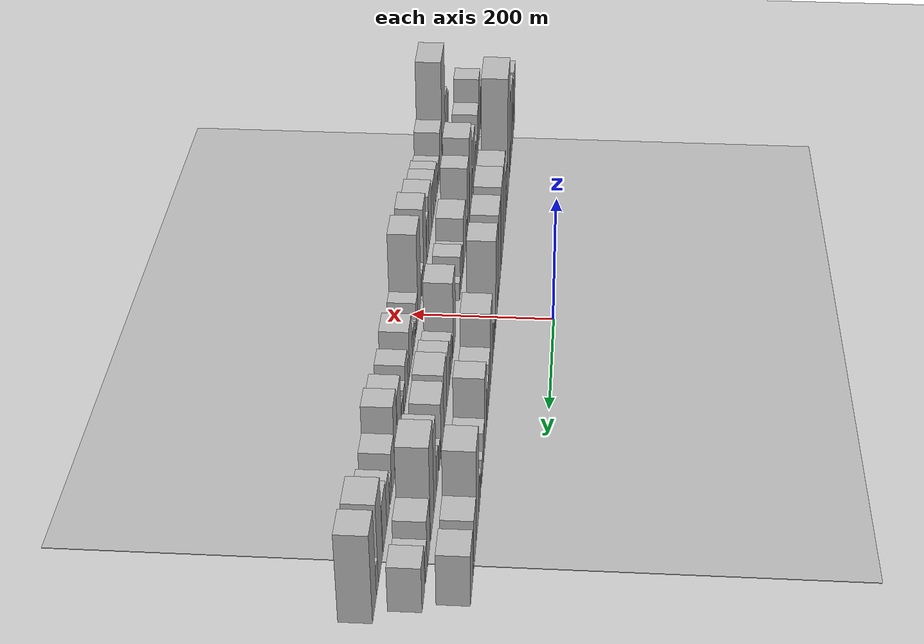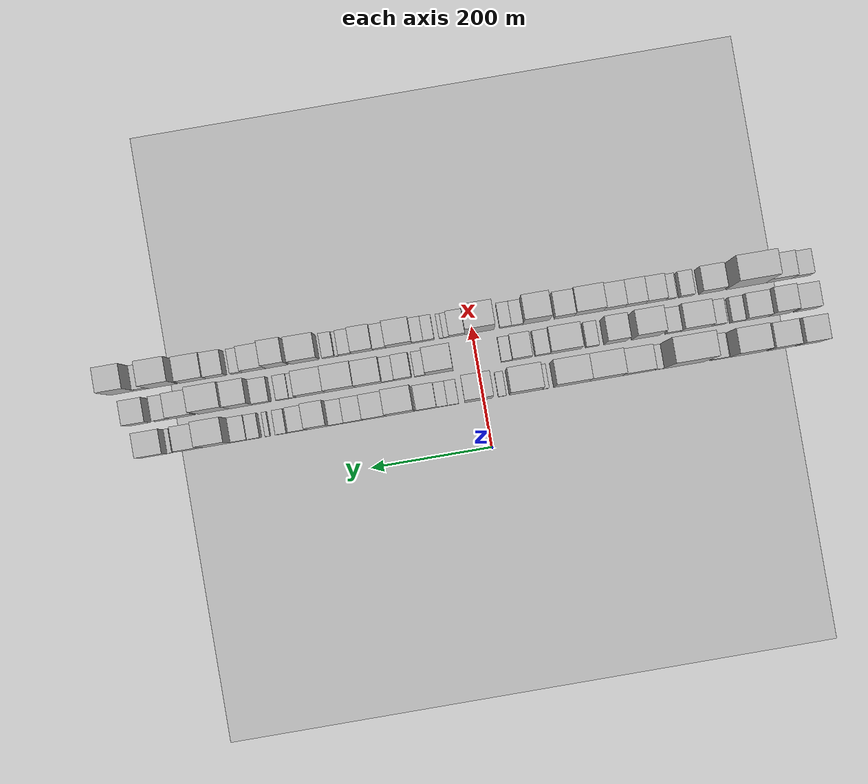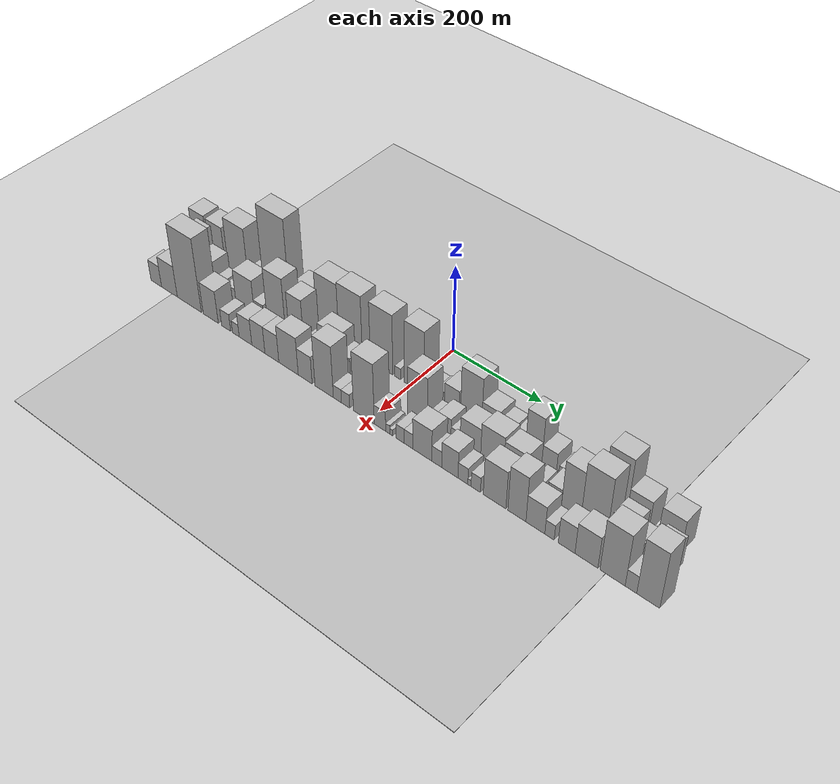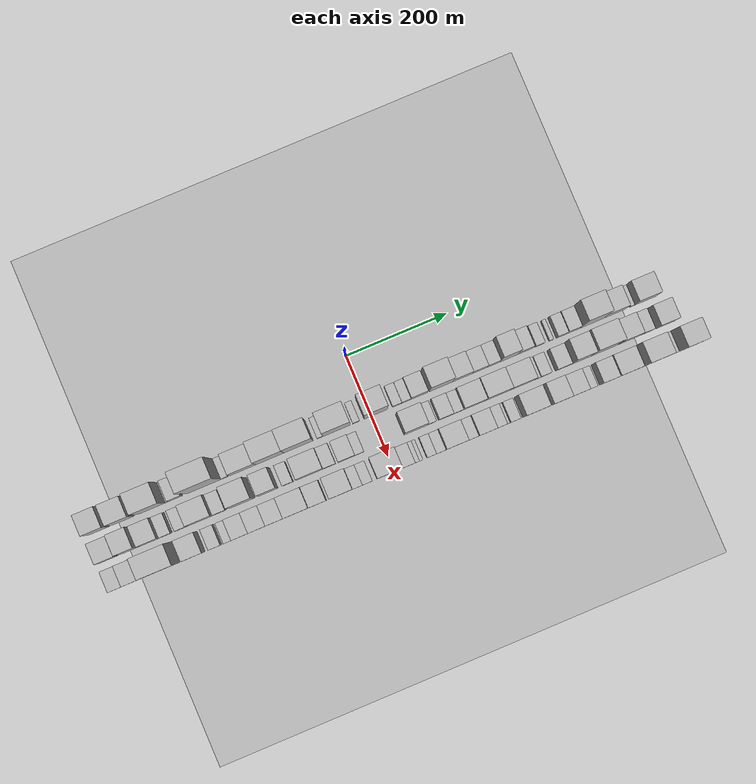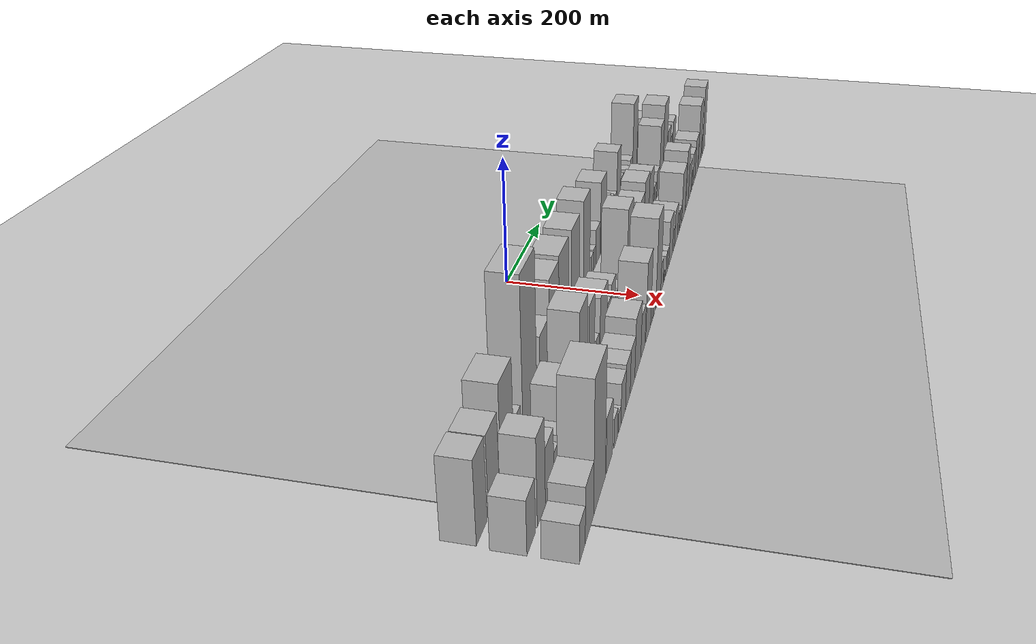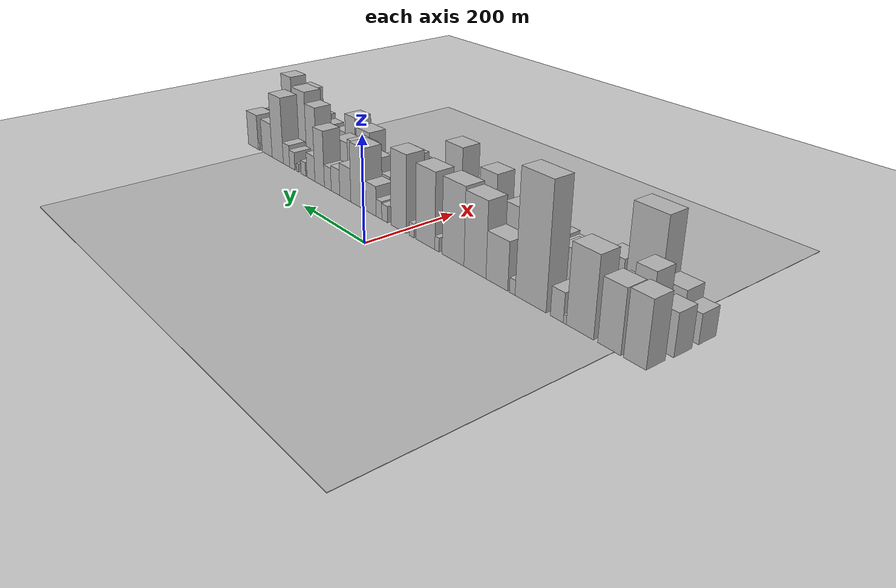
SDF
<?xml version="1.0" encoding="utf-8"?>

<sdf version="1.6">

   <world name="default">

      <gui fullscreen="0">

         <camera name="user_camera">

            <pose>-15 0 4.57585 0 0 0</pose>

            <view_controller>orbit</view_controller>

         </camera>

      </gui>

      <scene>

         <sky>

           <clouds>

             <speed>12</speed>

           </clouds>

         </sky>

         <ambient>0.4 0.4 0.4 1</ambient>

         <background>0.7 0.7 0.7 1</background>

         <shadows>1</shadows>

      </scene>

      <gravity>0 0 -9.8066</gravity>

      <magnetic_field>6e-06 2.3e-05 -4.2e-05</magnetic_field>

      <physics default="0" name="default_physics" type="ode">

         <ode>

            <solver>

               <type>quick</type>

               <iters>10</iters>

               <sor>1.0</sor>

               <use_dynamic_moi_rescaling>0</use_dynamic_moi_rescaling>

            </solver>

            <constraints>

               <cfm>0</cfm>

               <erp>0.2</erp>

               <contact_max_correcting_vel>100</contact_max_correcting_vel>

               <contact_surface_layer>0.001</contact_surface_layer>

            </constraints>

         </ode>

         <max_step_size>0.004</max_step_size>

         <real_time_factor>1</real_time_factor>

         <real_time_update_rate>250</real_time_update_rate>

      </physics>

      <light name="sun" type="directional">

         <cast_shadows>1</cast_shadows>

         <pose>0 0 10 0 0 0</pose>

         <diffuse>0.8 0.8 0.8 1</diffuse>

         <specular>0.2 0.2 0.2 1</specular>

         <attenuation>

            <range>1000</range>

            <constant>0.9</constant>

            <linear>0.01</linear>

            <quadratic>0.001</quadratic>

         </attenuation>

         <direction>-0.5 0.1 -0.9</direction>

      </light>

      <include>

         <name>ground_plane_1</name>

         <uri>model://HANNAS_ground_plane</uri>

         <pose>0 0 0  0 0 0</pose>

      </include>

      <include>

         <name>ground_plane_2</name>

         <uri>model://HANNAS_ground_plane</uri>

         <pose>100 0 0  0 0 0</pose>

      </include>

      <model name="building_1">

         <static>1</static>

         <pose frame="">100.0000 -536.8642 0 0.000000 0.000000 0.000000</pose>

         <link name="link">

            <pose frame="">0 0 55.50 0 0 0</pose>

            <collision name="collision">

               <geometry>

                  <box>

                     <size>40.0000 40.2715 111.0000</size>

                  </box>

               </geometry>

               <max_contacts>10</max_contacts>

               <surface>

                  <contact>

                     <ode/>

                  </contact>

                  <bounce/>

                  <friction>

                     <torsional>

                        <ode/>

                     </torsional>

                     <ode/>

                  </friction>

               </surface>

            </collision>

            <visual name="visual">

               <cast_shadows>0</cast_shadows>

               <geometry>

                  <box>

                     <size>40.0000 40.2715 111.0000</size>

                  </box>

               </geometry>

               <material>

                  <script>

                     <uri>model://HANNAS_wall/materials/scripts</uri>

                     <uri>model://HANNAS_wall/materials/textures</uri>

                     <name>vrc/HANNAS_wall</name>

                  </script>

               </material>

            </visual>

            <self_collide>0</self_collide>

            <enable_wind>0</enable_wind>

            <kinematic>0</kinematic>

         </link>

      </model>

      <model name="building_2">

         <static>1</static>

         <pose frame="">100.0000 -490.1506 0 0.000000 0.000000 0.000000</pose>

         <link name="link">

            <pose frame="">0 0 54.00 0 0 0</pose>

            <collision name="collision">

               <geometry>

                  <box>

                     <size>40.0000 43.1557 108.0000</size>

                  </box>

               </geometry>

               <max_contacts>10</max_contacts>

               <surface>

                  <contact>

                     <ode/>

                  </contact>

                  <bounce/>

                  <friction>

                     <torsional>

                        <ode/>

                     </torsional>

                     <ode/>

                  </friction>

               </surface>

            </collision>

            <visual name="visual">

               <cast_shadows>0</cast_shadows>

               <geometry>

                  <box>

                     <size>40.0000 43.1557 108.0000</size>

                  </box>

               </geometry>

               <material>

                  <script>

                     <uri>model://HANNAS_wall/materials/scripts</uri>

                     <uri>model://HANNAS_wall/materials/textures</uri>

                     <name>vrc/HANNAS_wall</name>

                  </script>

               </material>

            </visual>

            <self_collide>0</self_collide>

            <enable_wind>0</enable_wind>

            <kinematic>0</kinematic>

         </link>

      </model>

      <model name="building_3">

         <static>1</static>

         <pose frame="">100.0000 -433.5643 0 0.000000 0.000000 0.000000</pose>

         <link name="link">

            <pose frame="">0 0 69.00 0 0 0</pose>

            <collision name="collision">

               <geometry>

                  <box>

                     <size>40.0000 54.0171 138.0000</size>

                  </box>

               </geometry>

               <max_contacts>10</max_contacts>

               <surface>

                  <contact>

                     <ode/>

                  </contact>

                  <bounce/>

                  <friction>

                     <torsional>

                        <ode/>

                     </torsional>

                     <ode/>

                  </friction>

               </surface>

            </collision>

            <visual name="visual">

               <cast_shadows>0</cast_shadows>

               <geometry>

                  <box>

                     <size>40.0000 54.0171 138.0000</size>

                  </box>

               </geometry>

               <material>

                  <script>

                     <uri>model://HANNAS_wall/materials/scripts</uri>

                     <uri>model://HANNAS_wall/materials/textures</uri>

                     <name>vrc/HANNAS_wall</name>

                  </script>

               </material>

            </visual>

            <self_collide>0</self_collide>

            <enable_wind>0</enable_wind>

            <kinematic>0</kinematic>

         </link>

      </model>

      <model name="building_4">

         <static>1</static>

         <pose frame="">100.0000 -403.4667 0 0.000000 0.000000 0.000000</pose>

         <link name="link">

            <pose frame="">0 0 7.50 0 0 0</pose>

            <collision name="collision">

               <geometry>

                  <box>

                     <size>40.0000 6.1781 15.0000</size>

                  </box>

               </geometry>

               <max_contacts>10</max_contacts>

               <surface>

                  <contact>

                     <ode/>

                  </contact>

                  <bounce/>

                  <friction>

                     <torsional>

                        <ode/>

                     </torsional>

                     <ode/>

                  </friction>

               </surface>

            </collision>

            <visual name="visual">

               <cast_shadows>0</cast_shadows>

               <geometry>

                  <box>

                     <size>40.0000 6.1781 15.0000</size>

                  </box>

               </geometry>

               <material>

                  <script>

                     <uri>model://HANNAS_wall/materials/scripts</uri>

                     <uri>model://HANNAS_wall/materials/textures</uri>

                     <name>vrc/HANNAS_wall</name>

                  </script>

               </material>

            </visual>

            <self_collide>0</self_collide>

            <enable_wind>0</enable_wind>

            <kinematic>0</kinematic>

         </link>

      </model>

      <model name="building_5">

         <static>1</static>

         <pose frame="">100.0000 -386.9525 0 0.000000 0.000000 0.000000</pose>

         <link name="link">

            <pose frame="">0 0 25.50 0 0 0</pose>

            <collision name="collision">

               <geometry>

                  <box>

                     <size>40.0000 26.8504 51.0000</size>

                  </box>

               </geometry>

               <max_contacts>10</max_contacts>

               <surface>

                  <contact>

                     <ode/>

                  </contact>

                  <bounce/>

                  <friction>

                     <torsional>

                        <ode/>

                     </torsional>

                     <ode/>

                  </friction>

               </surface>

            </collision>

            <visual name="visual">

               <cast_shadows>0</cast_shadows>

               <geometry>

                  <box>

                     <size>40.0000 26.8504 51.0000</size>

                  </box>

               </geometry>

               <material>

                  <script>

                     <uri>model://HANNAS_wall/materials/scripts</uri>

                     <uri>model://HANNAS_wall/materials/textures</uri>

                     <name>vrc/HANNAS_wall</name>

                  </script>

               </material>

            </visual>

            <self_collide>0</self_collide>

            <enable_wind>0</enable_wind>

            <kinematic>0</kinematic>

         </link>

      </model>

      <model name="building_6">

         <static>1</static>

         <pose frame="">100.0000 -330.4034 0 0.000000 0.000000 0.000000</pose>

         <link name="link">

            <pose frame="">0 0 109.50 0 0 0</pose>

            <collision name="collision">

               <geometry>

                  <box>

                     <size>40.0000 68.2477 219.0000</size>

                  </box>

               </geometry>

               <max_contacts>10</max_contacts>

               <surface>

                  <contact>

                     <ode/>

                  </contact>

                  <bounce/>

                  <friction>

                     <torsional>

                        <ode/>

                     </torsional>

                     <ode/>

                  </friction>

               </surface>

            </collision>

            <visual name="visual">

               <cast_shadows>0</cast_shadows>

               <geometry>

                  <box>

                     <size>40.0000 68.2477 219.0000</size>

                  </box>

               </geometry>

               <material>

                  <script>

                     <uri>model://HANNAS_wall/materials/scripts</uri>

                     <uri>model://HANNAS_wall/materials/textures</uri>

                     <name>vrc/HANNAS_wall</name>

                  </script>

               </material>

            </visual>

            <self_collide>0</self_collide>

            <enable_wind>0</enable_wind>

            <kinematic>0</kinematic>

         </link>

      </model>

      <model name="building_7">

         <static>1</static>

         <pose frame="">100.0000 -289.7703 0 0.000000 0.000000 0.000000</pose>

         <link name="link">

            <pose frame="">0 0 13.50 0 0 0</pose>

            <collision name="collision">

               <geometry>

                  <box>

                     <size>40.0000 13.0185 27.0000</size>

                  </box>

               </geometry>

               <max_contacts>10</max_contacts>

               <surface>

                  <contact>

                     <ode/>

                  </contact>

                  <bounce/>

                  <friction>

                     <torsional>

                        <ode/>

                     </torsional>

                     <ode/>

                  </friction>

               </surface>

            </collision>

            <visual name="visual">

               <cast_shadows>0</cast_shadows>

               <geometry>

                  <box>

                     <size>40.0000 13.0185 27.0000</size>

                  </box>

               </geometry>

               <material>

                  <script>

                     <uri>model://HANNAS_wall/materials/scripts</uri>

                     <uri>model://HANNAS_wall/materials/textures</uri>

                     <name>vrc/HANNAS_wall</name>

                  </script>

               </material>

            </visual>

            <self_collide>0</self_collide>

            <enable_wind>0</enable_wind>

            <kinematic>0</kinematic>

         </link>

      </model>

      <model name="building_8">

         <static>1</static>

         <pose frame="">100.0000 -253.4309 0 0.000000 0.000000 0.000000</pose>

         <link name="link">

            <pose frame="">0 0 43.50 0 0 0</pose>

            <collision name="collision">

               <geometry>

                  <box>

                     <size>40.0000 51.6604 87.0000</size>

                  </box>

               </geometry>

               <max_contacts>10</max_contacts>

               <surface>

                  <contact>

                     <ode/>

                  </contact>

                  <bounce/>

                  <friction>

                     <torsional>

                        <ode/>

                     </torsional>

                     <ode/>

                  </friction>

               </surface>

            </collision>

            <visual name="visual">

               <cast_shadows>0</cast_shadows>

               <geometry>

                  <box>

                     <size>40.0000 51.6604 87.0000</size>

                  </box>

               </geometry>

               <material>

                  <script>

                     <uri>model://HANNAS_wall/materials/scripts</uri>

                     <uri>model://HANNAS_wall/materials/textures</uri>

                     <name>vrc/HANNAS_wall</name>

                  </script>

               </material>

            </visual>

            <self_collide>0</self_collide>

            <enable_wind>0</enable_wind>

            <kinematic>0</kinematic>

         </link>

      </model>

      <model name="building_9">

         <static>1</static>

         <pose frame="">100.0000 -200.1595 0 0.000000 0.000000 0.000000</pose>

         <link name="link">

            <pose frame="">0 0 69.00 0 0 0</pose>

            <collision name="collision">

               <geometry>

                  <box>

                     <size>40.0000 54.8824 138.0000</size>

                  </box>

               </geometry>

               <max_contacts>10</max_contacts>

               <surface>

                  <contact>

                     <ode/>

                  </contact>

                  <bounce/>

                  <friction>

                     <torsional>

                        <ode/>

                     </torsional>

                     <ode/>

                  </friction>

               </surface>

            </collision>

            <visual name="visual">

               <cast_shadows>0</cast_shadows>

               <geometry>

                  <box>

                     <size>40.0000 54.8824 138.0000</size>

                  </box>

               </geometry>

               <material>

                  <script>

                     <uri>model://HANNAS_wall/materials/scripts</uri>

                     <uri>model://HANNAS_wall/materials/textures</uri>

                     <name>vrc/HANNAS_wall</name>

                  </script>

               </material>

            </visual>

            <self_collide>0</self_collide>

            <enable_wind>0</enable_wind>

            <kinematic>0</kinematic>

         </link>

      </model>

      <model name="building_10">

         <static>1</static>

         <pose frame="">100.0000 -143.9426 0 0.000000 0.000000 0.000000</pose>

         <link name="link">

            <pose frame="">0 0 72.00 0 0 0</pose>

            <collision name="collision">

               <geometry>

                  <box>

                     <size>40.0000 57.5515 144.0000</size>

                  </box>

               </geometry>

               <max_contacts>10</max_contacts>

               <surface>

                  <contact>

                     <ode/>

                  </contact>

                  <bounce/>

                  <friction>

                     <torsional>

                        <ode/>

                     </torsional>

                     <ode/>

                  </friction>

               </surface>

            </collision>

            <visual name="visual">

               <cast_shadows>0</cast_shadows>

               <geometry>

                  <box>

                     <size>40.0000 57.5515 144.0000</size>

                  </box>

               </geometry>

               <material>

                  <script>

                     <uri>model://HANNAS_wall/materials/scripts</uri>

                     <uri>model://HANNAS_wall/materials/textures</uri>

                     <name>vrc/HANNAS_wall</name>

                  </script>

               </material>

            </visual>

            <self_collide>0</self_collide>

            <enable_wind>0</enable_wind>

            <kinematic>0</kinematic>

         </link>

      </model>

      <model name="building_11">

         <static>1</static>

         <pose frame="">100.0000 -101.3857 0 0.000000 0.000000 0.000000</pose>

         <link name="link">

            <pose frame="">0 0 13.50 0 0 0</pose>

            <collision name="collision">

               <geometry>

                  <box>

                     <size>40.0000 11.5622 27.0000</size>

                  </box>

               </geometry>

               <max_contacts>10</max_contacts>

               <surface>

                  <contact>

                     <ode/>

                  </contact>

                  <bounce/>

                  <friction>

                     <torsional>

                        <ode/>

                     </torsional>

                     <ode/>

                  </friction>

               </surface>

            </collision>

            <visual name="visual">

               <cast_shadows>0</cast_shadows>

               <geometry>

                  <box>

                     <size>40.0000 11.5622 27.0000</size>

                  </box>

               </geometry>

               <material>

                  <script>

                     <uri>model://HANNAS_wall/materials/scripts</uri>

                     <uri>model://HANNAS_wall/materials/textures</uri>

                     <name>vrc/HANNAS_wall</name>

                  </script>

               </material>

            </visual>

            <self_collide>0</self_collide>

            <enable_wind>0</enable_wind>

            <kinematic>0</kinematic>

         </link>

      </model>

      <model name="building_12">

         <static>1</static>

         <pose frame="">100.0000 -68.6896 0 0.000000 0.000000 0.000000</pose>

         <link name="link">

            <pose frame="">0 0 72.00 0 0 0</pose>

            <collision name="collision">

               <geometry>

                  <box>

                     <size>40.0000 53.8299 144.0000</size>

                  </box>

               </geometry>

               <max_contacts>10</max_contacts>

               <surface>

                  <contact>

                     <ode/>

                  </contact>

                  <bounce/>

                  <friction>

                     <torsional>

                        <ode/>

                     </torsional>

                     <ode/>

                  </friction>

               </surface>

            </collision>

            <visual name="visual">

               <cast_shadows>0</cast_shadows>

               <geometry>

                  <box>

                     <size>40.0000 53.8299 144.0000</size>

                  </box>

               </geometry>

               <material>

                  <script>

                     <uri>model://HANNAS_wall/materials/scripts</uri>

                     <uri>model://HANNAS_wall/materials/textures</uri>

                     <name>vrc/HANNAS_wall</name>

                  </script>

               </material>

            </visual>

            <self_collide>0</self_collide>

            <enable_wind>0</enable_wind>

            <kinematic>0</kinematic>

         </link>

      </model>

      <model name="building_13">

         <static>1</static>

         <pose frame="">100.0000 -30.1146 0 0.000000 0.000000 0.000000</pose>

         <link name="link">

            <pose frame="">0 0 13.50 0 0 0</pose>

            <collision name="collision">

               <geometry>

                  <box>

                     <size>40.0000 13.3202 27.0000</size>

                  </box>

               </geometry>

               <max_contacts>10</max_contacts>

               <surface>

                  <contact>

                     <ode/>

                  </contact>

                  <bounce/>

                  <friction>

                     <torsional>

                        <ode/>

                     </torsional>

                     <ode/>

                  </friction>

               </surface>

            </collision>

            <visual name="visual">

               <cast_shadows>0</cast_shadows>

               <geometry>

                  <box>

                     <size>40.0000 13.3202 27.0000</size>

                  </box>

               </geometry>

               <material>

                  <script>

                     <uri>model://HANNAS_wall/materials/scripts</uri>

                     <uri>model://HANNAS_wall/materials/textures</uri>

                     <name>vrc/HANNAS_wall</name>

                  </script>

               </material>

            </visual>

            <self_collide>0</self_collide>

            <enable_wind>0</enable_wind>

            <kinematic>0</kinematic>

         </link>

      </model>

      <model name="building_14">

         <static>1</static>

         <pose frame="">100.0000 8.6162 0 0.000000 0.000000 0.000000</pose>

         <link name="link">

            <pose frame="">0 0 75.00 0 0 0</pose>

            <collision name="collision">

               <geometry>

                  <box>

                     <size>40.0000 46.1414 150.0000</size>

                  </box>

               </geometry>

               <max_contacts>10</max_contacts>

               <surface>

                  <contact>

                     <ode/>

                  </contact>

                  <bounce/>

                  <friction>

                     <torsional>

                        <ode/>

                     </torsional>

                     <ode/>

                  </friction>

               </surface>

            </collision>

            <visual name="visual">

               <cast_shadows>0</cast_shadows>

               <geometry>

                  <box>

                     <size>40.0000 46.1414 150.0000</size>

                  </box>

               </geometry>

               <material>

                  <script>

                     <uri>model://HANNAS_wall/materials/scripts</uri>

                     <uri>model://HANNAS_wall/materials/textures</uri>

                     <name>vrc/HANNAS_wall</name>

                  </script>

               </material>

            </visual>

            <self_collide>0</self_collide>

            <enable_wind>0</enable_wind>

            <kinematic>0</kinematic>

         </link>

      </model>

      <model name="building_15">

         <static>1</static>

         <pose frame="">100.0000 50.8726 0 0.000000 0.000000 0.000000</pose>

         <link name="link">

            <pose frame="">0 0 16.50 0 0 0</pose>

            <collision name="collision">

               <geometry>

                  <box>

                     <size>40.0000 18.3715 33.0000</size>

                  </box>

               </geometry>

               <max_contacts>10</max_contacts>

               <surface>

                  <contact>

                     <ode/>

                  </contact>

                  <bounce/>

                  <friction>

                     <torsional>

                        <ode/>

                     </torsional>

                     <ode/>

                  </friction>

               </surface>

            </collision>

            <visual name="visual">

               <cast_shadows>0</cast_shadows>

               <geometry>

                  <box>

                     <size>40.0000 18.3715 33.0000</size>

                  </box>

               </geometry>

               <material>

                  <script>

                     <uri>model://HANNAS_wall/materials/scripts</uri>

                     <uri>model://HANNAS_wall/materials/textures</uri>

                     <name>vrc/HANNAS_wall</name>

                  </script>

               </material>

            </visual>

            <self_collide>0</self_collide>

            <enable_wind>0</enable_wind>

            <kinematic>0</kinematic>

         </link>

      </model>

      <model name="building_16">

         <static>1</static>

         <pose frame="">100.0000 69.0831 0 0.000000 0.000000 0.000000</pose>

         <link name="link">

            <pose frame="">0 0 18.00 0 0 0</pose>

            <collision name="collision">

               <geometry>

                  <box>

                     <size>40.0000 18.0495 36.0000</size>

                  </box>

               </geometry>

               <max_contacts>10</max_contacts>

               <surface>

                  <contact>

                     <ode/>

                  </contact>

                  <bounce/>

                  <friction>

                     <torsional>

                        <ode/>

                     </torsional>

                     <ode/>

                  </friction>

               </surface>

            </collision>

            <visual name="visual">

               <cast_shadows>0</cast_shadows>

               <geometry>

                  <box>

                     <size>40.0000 18.0495 36.0000</size>

                  </box>

               </geometry>

               <material>

                  <script>

                     <uri>model://HANNAS_wall/materials/scripts</uri>

                     <uri>model://HANNAS_wall/materials/textures</uri>

                     <name>vrc/HANNAS_wall</name>

                  </script>

               </material>

            </visual>

            <self_collide>0</self_collide>

            <enable_wind>0</enable_wind>

            <kinematic>0</kinematic>

         </link>

      </model>

      <model name="building_17">

         <static>1</static>

         <pose frame="">100.0000 94.7705 0 0.000000 0.000000 0.000000</pose>

         <link name="link">

            <pose frame="">0 0 30.00 0 0 0</pose>

            <collision name="collision">

               <geometry>

                  <box>

                     <size>40.0000 33.3253 60.0000</size>

                  </box>

               </geometry>

               <max_contacts>10</max_contacts>

               <surface>

                  <contact>

                     <ode/>

                  </contact>

                  <bounce/>

                  <friction>

                     <torsional>

                        <ode/>

                     </torsional>

                     <ode/>

                  </friction>

               </surface>

            </collision>

            <visual name="visual">

               <cast_shadows>0</cast_shadows>

               <geometry>

                  <box>

                     <size>40.0000 33.3253 60.0000</size>

                  </box>

               </geometry>

               <material>

                  <script>

                     <uri>model://HANNAS_wall/materials/scripts</uri>

                     <uri>model://HANNAS_wall/materials/textures</uri>

                     <name>vrc/HANNAS_wall</name>

                  </script>

               </material>

            </visual>

            <self_collide>0</self_collide>

            <enable_wind>0</enable_wind>

            <kinematic>0</kinematic>

         </link>

      </model>

      <model name="building_18">

         <static>1</static>

         <pose frame="">100.0000 137.8663 0 0.000000 0.000000 0.000000</pose>

         <link name="link">

            <pose frame="">0 0 61.50 0 0 0</pose>

            <collision name="collision">

               <geometry>

                  <box>

                     <size>40.0000 46.8662 123.0000</size>

                  </box>

               </geometry>

               <max_contacts>10</max_contacts>

               <surface>

                  <contact>

                     <ode/>

                  </contact>

                  <bounce/>

                  <friction>

                     <torsional>

                        <ode/>

                     </torsional>

                     <ode/>

                  </friction>

               </surface>

            </collision>

            <visual name="visual">

               <cast_shadows>0</cast_shadows>

               <geometry>

                  <box>

                     <size>40.0000 46.8662 123.0000</size>

                  </box>

               </geometry>

               <material>

                  <script>

                     <uri>model://HANNAS_wall/materials/scripts</uri>

                     <uri>model://HANNAS_wall/materials/textures</uri>

                     <name>vrc/HANNAS_wall</name>

                  </script>

               </material>

            </visual>

            <self_collide>0</self_collide>

            <enable_wind>0</enable_wind>

            <kinematic>0</kinematic>

         </link>

      </model>

      <model name="building_19">

         <static>1</static>

         <pose frame="">100.0000 180.4211 0 0.000000 0.000000 0.000000</pose>

         <link name="link">

            <pose frame="">0 0 34.50 0 0 0</pose>

            <collision name="collision">

               <geometry>

                  <box>

                     <size>40.0000 38.2435 69.0000</size>

                  </box>

               </geometry>

               <max_contacts>10</max_contacts>

               <surface>

                  <contact>

                     <ode/>

                  </contact>

                  <bounce/>

                  <friction>

                     <torsional>

                        <ode/>

                     </torsional>

                     <ode/>

                  </friction>

               </surface>

            </collision>

            <visual name="visual">

               <cast_shadows>0</cast_shadows>

               <geometry>

                  <box>

                     <size>40.0000 38.2435 69.0000</size>

                  </box>

               </geometry>

               <material>

                  <script>

                     <uri>model://HANNAS_wall/materials/scripts</uri>

                     <uri>model://HANNAS_wall/materials/textures</uri>

                     <name>vrc/HANNAS_wall</name>

                  </script>

               </material>

            </visual>

            <self_collide>0</self_collide>

            <enable_wind>0</enable_wind>

            <kinematic>0</kinematic>

         </link>

      </model>

      <model name="building_20">

         <static>1</static>

         <pose frame="">100.0000 214.7776 0 0.000000 0.000000 0.000000</pose>

         <link name="link">

            <pose frame="">0 0 27.00 0 0 0</pose>

            <collision name="collision">

               <geometry>

                  <box>

                     <size>40.0000 30.4695 54.0000</size>

                  </box>

               </geometry>

               <max_contacts>10</max_contacts>

               <surface>

                  <contact>

                     <ode/>

                  </contact>

                  <bounce/>

                  <friction>

                     <torsional>

                        <ode/>

                     </torsional>

                     <ode/>

                  </friction>

               </surface>

            </collision>

            <visual name="visual">

               <cast_shadows>0</cast_shadows>

               <geometry>

                  <box>

                     <size>40.0000 30.4695 54.0000</size>

                  </box>

               </geometry>

               <material>

                  <script>

                     <uri>model://HANNAS_wall/materials/scripts</uri>

                     <uri>model://HANNAS_wall/materials/textures</uri>

                     <name>vrc/HANNAS_wall</name>

                  </script>

               </material>

            </visual>

            <self_collide>0</self_collide>

            <enable_wind>0</enable_wind>

            <kinematic>0</kinematic>

         </link>

      </model>

      <model name="building_21">

         <static>1</static>

         <pose frame="">100.0000 242.4147 0 0.000000 0.000000 0.000000</pose>

         <link name="link">

            <pose frame="">0 0 24.00 0 0 0</pose>

            <collision name="collision">

               <geometry>

                  <box>

                     <size>40.0000 24.8045 48.0000</size>

                  </box>

               </geometry>

               <max_contacts>10</max_contacts>

               <surface>

                  <contact>

                     <ode/>

                  </contact>

                  <bounce/>

                  <friction>

                     <torsional>

                        <ode/>

                     </torsional>

                     <ode/>

                  </friction>

               </surface>

            </collision>

            <visual name="visual">

               <cast_shadows>0</cast_shadows>

               <geometry>

                  <box>

                     <size>40.0000 24.8045 48.0000</size>

                  </box>

               </geometry>

               <material>

                  <script>

                     <uri>model://HANNAS_wall/materials/scripts</uri>

                     <uri>model://HANNAS_wall/materials/textures</uri>

                     <name>vrc/HANNAS_wall</name>

                  </script>

               </material>

            </visual>

            <self_collide>0</self_collide>

            <enable_wind>0</enable_wind>

            <kinematic>0</kinematic>

         </link>

      </model>

      <model name="building_22">

         <static>1</static>

         <pose frame="">100.0000 272.4213 0 0.000000 0.000000 0.000000</pose>

         <link name="link">

            <pose frame="">0 0 58.50 0 0 0</pose>

            <collision name="collision">

               <geometry>

                  <box>

                     <size>40.0000 35.2088 117.0000</size>

                  </box>

               </geometry>

               <max_contacts>10</max_contacts>

               <surface>

                  <contact>

                     <ode/>

                  </contact>

                  <bounce/>

                  <friction>

                     <torsional>

                        <ode/>

                     </torsional>

                     <ode/>

                  </friction>

               </surface>

            </collision>

            <visual name="visual">

               <cast_shadows>0</cast_shadows>

               <geometry>

                  <box>

                     <size>40.0000 35.2088 117.0000</size>

                  </box>

               </geometry>

               <material>

                  <script>

                     <uri>model://HANNAS_wall/materials/scripts</uri>

                     <uri>model://HANNAS_wall/materials/textures</uri>

                     <name>vrc/HANNAS_wall</name>

                  </script>

               </material>

            </visual>

            <self_collide>0</self_collide>

            <enable_wind>0</enable_wind>

            <kinematic>0</kinematic>

         </link>

      </model>

      <model name="building_23">

         <static>1</static>

         <pose frame="">100.0000 305.1932 0 0.000000 0.000000 0.000000</pose>

         <link name="link">

            <pose frame="">0 0 27.00 0 0 0</pose>

            <collision name="collision">

               <geometry>

                  <box>

                     <size>40.0000 30.3350 54.0000</size>

                  </box>

               </geometry>

               <max_contacts>10</max_contacts>

               <surface>

                  <contact>

                     <ode/>

                  </contact>

                  <bounce/>

                  <friction>

                     <torsional>

                        <ode/>

                     </torsional>

                     <ode/>

                  </friction>

               </surface>

            </collision>

            <visual name="visual">

               <cast_shadows>0</cast_shadows>

               <geometry>

                  <box>

                     <size>40.0000 30.3350 54.0000</size>

                  </box>

               </geometry>

               <material>

                  <script>

                     <uri>model://HANNAS_wall/materials/scripts</uri>

                     <uri>model://HANNAS_wall/materials/textures</uri>

                     <name>vrc/HANNAS_wall</name>

                  </script>

               </material>

            </visual>

            <self_collide>0</self_collide>

            <enable_wind>0</enable_wind>

            <kinematic>0</kinematic>

         </link>

      </model>

      <model name="building_24">

         <static>1</static>

         <pose frame="">100.0000 334.2420 0 0.000000 0.000000 0.000000</pose>

         <link name="link">

            <pose frame="">0 0 15.00 0 0 0</pose>

            <collision name="collision">

               <geometry>

                  <box>

                     <size>40.0000 17.7624 30.0000</size>

                  </box>

               </geometry>

               <max_contacts>10</max_contacts>

               <surface>

                  <contact>

                     <ode/>

                  </contact>

                  <bounce/>

                  <friction>

                     <torsional>

                        <ode/>

                     </torsional>

                     <ode/>

                  </friction>

               </surface>

            </collision>

            <visual name="visual">

               <cast_shadows>0</cast_shadows>

               <geometry>

                  <box>

                     <size>40.0000 17.7624 30.0000</size>

                  </box>

               </geometry>

               <material>

                  <script>

                     <uri>model://HANNAS_wall/materials/scripts</uri>

                     <uri>model://HANNAS_wall/materials/textures</uri>

                     <name>vrc/HANNAS_wall</name>

                  </script>

               </material>

            </visual>

            <self_collide>0</self_collide>

            <enable_wind>0</enable_wind>

            <kinematic>0</kinematic>

         </link>

      </model>

      <model name="building_25">

         <static>1</static>

         <pose frame="">100.0000 357.0527 0 0.000000 0.000000 0.000000</pose>

         <link name="link">

            <pose frame="">0 0 9.00 0 0 0</pose>

            <collision name="collision">

               <geometry>

                  <box>

                     <size>40.0000 7.8591 18.0000</size>

                  </box>

               </geometry>

               <max_contacts>10</max_contacts>

               <surface>

                  <contact>

                     <ode/>

                  </contact>

                  <bounce/>

                  <friction>

                     <torsional>

                        <ode/>

                     </torsional>

                     <ode/>

                  </friction>

               </surface>

            </collision>

            <visual name="visual">

               <cast_shadows>0</cast_shadows>

               <geometry>

                  <box>

                     <size>40.0000 7.8591 18.0000</size>

                  </box>

               </geometry>

               <material>

                  <script>

                     <uri>model://HANNAS_wall/materials/scripts</uri>

                     <uri>model://HANNAS_wall/materials/textures</uri>

                     <name>vrc/HANNAS_wall</name>

                  </script>

               </material>

            </visual>

            <self_collide>0</self_collide>

            <enable_wind>0</enable_wind>

            <kinematic>0</kinematic>

         </link>

      </model>

      <model name="building_26">

         <static>1</static>

         <pose frame="">100.0000 378.4067 0 0.000000 0.000000 0.000000</pose>

         <link name="link">

            <pose frame="">0 0 19.50 0 0 0</pose>

            <collision name="collision">

               <geometry>

                  <box>

                     <size>40.0000 20.8488 39.0000</size>

                  </box>

               </geometry>

               <max_contacts>10</max_contacts>

               <surface>

                  <contact>

                     <ode/>

                  </contact>

                  <bounce/>

                  <friction>

                     <torsional>

                        <ode/>

                     </torsional>

                     <ode/>

                  </friction>

               </surface>

            </collision>

            <visual name="visual">

               <cast_shadows>0</cast_shadows>

               <geometry>

                  <box>

                     <size>40.0000 20.8488 39.0000</size>

                  </box>

               </geometry>

               <material>

                  <script>

                     <uri>model://HANNAS_wall/materials/scripts</uri>

                     <uri>model://HANNAS_wall/materials/textures</uri>

                     <name>vrc/HANNAS_wall</name>

                  </script>

               </material>

            </visual>

            <self_collide>0</self_collide>

            <enable_wind>0</enable_wind>

            <kinematic>0</kinematic>

         </link>

      </model>

      <model name="building_27">

         <static>1</static>

         <pose frame="">100.0000 401.6631 0 0.000000 0.000000 0.000000</pose>

         <link name="link">

            <pose frame="">0 0 24.00 0 0 0</pose>

            <collision name="collision">

               <geometry>

                  <box>

                     <size>40.0000 25.6641 48.0000</size>

                  </box>

               </geometry>

               <max_contacts>10</max_contacts>

               <surface>

                  <contact>

                     <ode/>

                  </contact>

                  <bounce/>

                  <friction>

                     <torsional>

                        <ode/>

                     </torsional>

                     <ode/>

                  </friction>

               </surface>

            </collision>

            <visual name="visual">

               <cast_shadows>0</cast_shadows>

               <geometry>

                  <box>

                     <size>40.0000 25.6641 48.0000</size>

                  </box>

               </geometry>

               <material>

                  <script>

                     <uri>model://HANNAS_wall/materials/scripts</uri>

                     <uri>model://HANNAS_wall/materials/textures</uri>

                     <name>vrc/HANNAS_wall</name>

                  </script>

               </material>

            </visual>

            <self_collide>0</self_collide>

            <enable_wind>0</enable_wind>

            <kinematic>0</kinematic>

         </link>

      </model>

      <model name="building_28">

         <static>1</static>

         <pose frame="">100.0000 438.0764 0 0.000000 0.000000 0.000000</pose>

         <link name="link">

            <pose frame="">0 0 72.00 0 0 0</pose>

            <collision name="collision">

               <geometry>

                  <box>

                     <size>40.0000 47.1625 144.0000</size>

                  </box>

               </geometry>

               <max_contacts>10</max_contacts>

               <surface>

                  <contact>

                     <ode/>

                  </contact>

                  <bounce/>

                  <friction>

                     <torsional>

                        <ode/>

                     </torsional>

                     <ode/>

                  </friction>

               </surface>

            </collision>

            <visual name="visual">

               <cast_shadows>0</cast_shadows>

               <geometry>

                  <box>

                     <size>40.0000 47.1625 144.0000</size>

                  </box>

               </geometry>

               <material>

                  <script>

                     <uri>model://HANNAS_wall/materials/scripts</uri>

                     <uri>model://HANNAS_wall/materials/textures</uri>

                     <name>vrc/HANNAS_wall</name>

                  </script>

               </material>

            </visual>

            <self_collide>0</self_collide>

            <enable_wind>0</enable_wind>

            <kinematic>0</kinematic>

         </link>

      </model>

      <model name="building_29">

         <static>1</static>

         <pose frame="">100.0000 483.0915 0 0.000000 0.000000 0.000000</pose>

         <link name="link">

            <pose frame="">0 0 37.50 0 0 0</pose>

            <collision name="collision">

               <geometry>

                  <box>

                     <size>40.0000 42.8678 75.0000</size>

                  </box>

               </geometry>

               <max_contacts>10</max_contacts>

               <surface>

                  <contact>

                     <ode/>

                  </contact>

                  <bounce/>

                  <friction>

                     <torsional>

                        <ode/>

                     </torsional>

                     <ode/>

                  </friction>

               </surface>

            </collision>

            <visual name="visual">

               <cast_shadows>0</cast_shadows>

               <geometry>

                  <box>

                     <size>40.0000 42.8678 75.0000</size>

                  </box>

               </geometry>

               <material>

                  <script>

                     <uri>model://HANNAS_wall/materials/scripts</uri>

                     <uri>model://HANNAS_wall/materials/textures</uri>

                     <name>vrc/HANNAS_wall</name>

                  </script>

               </material>

            </visual>

            <self_collide>0</self_collide>

            <enable_wind>0</enable_wind>

            <kinematic>0</kinematic>

         </link>

      </model>

      <model name="building_30">

         <static>1</static>

         <pose frame="">100.0000 518.2733 0 0.000000 0.000000 0.000000</pose>

         <link name="link">

            <pose frame="">0 0 9.00 0 0 0</pose>

            <collision name="collision">

               <geometry>

                  <box>

                     <size>40.0000 7.4957 18.0000</size>

                  </box>

               </geometry>

               <max_contacts>10</max_contacts>

               <surface>

                  <contact>

                     <ode/>

                  </contact>

                  <bounce/>

                  <friction>

                     <torsional>

                        <ode/>

                     </torsional>

                     <ode/>

                  </friction>

               </surface>

            </collision>

            <visual name="visual">

               <cast_shadows>0</cast_shadows>

               <geometry>

                  <box>

                     <size>40.0000 7.4957 18.0000</size>

                  </box>

               </geometry>

               <material>

                  <script>

                     <uri>model://HANNAS_wall/materials/scripts</uri>

                     <uri>model://HANNAS_wall/materials/textures</uri>

                     <name>vrc/HANNAS_wall</name>

                  </script>

               </material>

            </visual>

            <self_collide>0</self_collide>

            <enable_wind>0</enable_wind>

            <kinematic>0</kinematic>

         </link>

      </model>

      <model name="building_31">

         <static>1</static>

         <pose frame="">100.0000 544.2316 0 0.000000 0.000000 0.000000</pose>

         <link name="link">

            <pose frame="">0 0 39.00 0 0 0</pose>

            <collision name="collision">

               <geometry>

                  <box>

                     <size>40.0000 44.4210 78.0000</size>

                  </box>

               </geometry>

               <max_contacts>10</max_contacts>

               <surface>

                  <contact>

                     <ode/>

                  </contact>

                  <bounce/>

                  <friction>

                     <torsional>

                        <ode/>

                     </torsional>

                     <ode/>

                  </friction>

               </surface>

            </collision>

            <visual name="visual">

               <cast_shadows>0</cast_shadows>

               <geometry>

                  <box>

                     <size>40.0000 44.4210 78.0000</size>

                  </box>

               </geometry>

               <material>

                  <script>

                     <uri>model://HANNAS_wall/materials/scripts</uri>

                     <uri>model://HANNAS_wall/materials/textures</uri>

                     <name>vrc/HANNAS_wall</name>

                  </script>

               </material>

            </visual>

            <self_collide>0</self_collide>

            <enable_wind>0</enable_wind>

            <kinematic>0</kinematic>

         </link>

      </model>

      <model name="building_32">

         <static>1</static>

         <pose frame="">155.0000 -541.5286 0 0.000000 0.000000 0.000000</pose>

         <link name="link">

            <pose frame="">0 0 36.00 0 0 0</pose>

            <collision name="collision">

               <geometry>

                  <box>

                     <size>40.0000 36.9427 72.0000</size>

                  </box>

               </geometry>

               <max_contacts>10</max_contacts>

               <surface>

                  <contact>

                     <ode/>

                  </contact>

                  <bounce/>

                  <friction>

                     <torsional>

                        <ode/>

                     </torsional>

                     <ode/>

                  </friction>

               </surface>

            </collision>

            <visual name="visual">

               <cast_shadows>0</cast_shadows>

               <geometry>

                  <box>

                     <size>40.0000 36.9427 72.0000</size>

                  </box>

               </geometry>

               <material>

                  <script>

                     <uri>model://HANNAS_wall/materials/scripts</uri>

                     <uri>model://HANNAS_wall/materials/textures</uri>

                     <name>vrc/HANNAS_wall</name>

                  </script>

               </material>

            </visual>

            <self_collide>0</self_collide>

            <enable_wind>0</enable_wind>

            <kinematic>0</kinematic>

         </link>

      </model>

      <model name="building_33">

         <static>1</static>

         <pose frame="">155.0000 -497.5827 0 0.000000 0.000000 0.000000</pose>

         <link name="link">

            <pose frame="">0 0 58.50 0 0 0</pose>

            <collision name="collision">

               <geometry>

                  <box>

                     <size>40.0000 36.9491 117.0000</size>

                  </box>

               </geometry>

               <max_contacts>10</max_contacts>

               <surface>

                  <contact>

                     <ode/>

                  </contact>

                  <bounce/>

                  <friction>

                     <torsional>

                        <ode/>

                     </torsional>

                     <ode/>

                  </friction>

               </surface>

            </collision>

            <visual name="visual">

               <cast_shadows>0</cast_shadows>

               <geometry>

                  <box>

                     <size>40.0000 36.9491 117.0000</size>

                  </box>

               </geometry>

               <material>

                  <script>

                     <uri>model://HANNAS_wall/materials/scripts</uri>

                     <uri>model://HANNAS_wall/materials/textures</uri>

                     <name>vrc/HANNAS_wall</name>

                  </script>

               </material>

            </visual>

            <self_collide>0</self_collide>

            <enable_wind>0</enable_wind>

            <kinematic>0</kinematic>

         </link>

      </model>

      <model name="building_34">

         <static>1</static>

         <pose frame="">155.0000 -459.2635 0 0.000000 0.000000 0.000000</pose>

         <link name="link">

            <pose frame="">0 0 37.50 0 0 0</pose>

            <collision name="collision">

               <geometry>

                  <box>

                     <size>40.0000 39.6893 75.0000</size>

                  </box>

               </geometry>

               <max_contacts>10</max_contacts>

               <surface>

                  <contact>

                     <ode/>

                  </contact>

                  <bounce/>

                  <friction>

                     <torsional>

                        <ode/>

                     </torsional>

                     <ode/>

                  </friction>

               </surface>

            </collision>

            <visual name="visual">

               <cast_shadows>0</cast_shadows>

               <geometry>

                  <box>

                     <size>40.0000 39.6893 75.0000</size>

                  </box>

               </geometry>

               <material>

                  <script>

                     <uri>model://HANNAS_wall/materials/scripts</uri>

                     <uri>model://HANNAS_wall/materials/textures</uri>

                     <name>vrc/HANNAS_wall</name>

                  </script>

               </material>

            </visual>

            <self_collide>0</self_collide>

            <enable_wind>0</enable_wind>

            <kinematic>0</kinematic>

         </link>

      </model>

      <model name="building_35">

         <static>1</static>

         <pose frame="">155.0000 -428.1269 0 0.000000 0.000000 0.000000</pose>

         <link name="link">

            <pose frame="">0 0 19.50 0 0 0</pose>

            <collision name="collision">

               <geometry>

                  <box>

                     <size>40.0000 22.5840 39.0000</size>

                  </box>

               </geometry>

               <max_contacts>10</max_contacts>

               <surface>

                  <contact>

                     <ode/>

                  </contact>

                  <bounce/>

                  <friction>

                     <torsional>

                        <ode/>

                     </torsional>

                     <ode/>

                  </friction>

               </surface>

            </collision>

            <visual name="visual">

               <cast_shadows>0</cast_shadows>

               <geometry>

                  <box>

                     <size>40.0000 22.5840 39.0000</size>

                  </box>

               </geometry>

               <material>

                  <script>

                     <uri>model://HANNAS_wall/materials/scripts</uri>

                     <uri>model://HANNAS_wall/materials/textures</uri>

                     <name>vrc/HANNAS_wall</name>

                  </script>

               </material>

            </visual>

            <self_collide>0</self_collide>

            <enable_wind>0</enable_wind>

            <kinematic>0</kinematic>

         </link>

      </model>

      <model name="building_36">

         <static>1</static>

         <pose frame="">155.0000 -396.2588 0 0.000000 0.000000 0.000000</pose>

         <link name="link">

            <pose frame="">0 0 21.00 0 0 0</pose>

            <collision name="collision">

               <geometry>

                  <box>

                     <size>40.0000 25.1522 42.0000</size>

                  </box>

               </geometry>

               <max_contacts>10</max_contacts>

               <surface>

                  <contact>

                     <ode/>

                  </contact>

                  <bounce/>

                  <friction>

                     <torsional>

                        <ode/>

                     </torsional>

                     <ode/>

                  </friction>

               </surface>

            </collision>

            <visual name="visual">

               <cast_shadows>0</cast_shadows>

               <geometry>

                  <box>

                     <size>40.0000 25.1522 42.0000</size>

                  </box>

               </geometry>

               <material>

                  <script>

                     <uri>model://HANNAS_wall/materials/scripts</uri>

                     <uri>model://HANNAS_wall/materials/textures</uri>

                     <name>vrc/HANNAS_wall</name>

                  </script>

               </material>

            </visual>

            <self_collide>0</self_collide>

            <enable_wind>0</enable_wind>

            <kinematic>0</kinematic>

         </link>

      </model>

      <model name="building_37">

         <static>1</static>

         <pose frame="">155.0000 -359.1557 0 0.000000 0.000000 0.000000</pose>

         <link name="link">

            <pose frame="">0 0 45.00 0 0 0</pose>

            <collision name="collision">

               <geometry>

                  <box>

                     <size>40.0000 49.0539 90.0000</size>

                  </box>

               </geometry>

               <max_contacts>10</max_contacts>

               <surface>

                  <contact>

                     <ode/>

                  </contact>

                  <bounce/>

                  <friction>

                     <torsional>

                        <ode/>

                     </torsional>

                     <ode/>

                  </friction>

               </surface>

            </collision>

            <visual name="visual">

               <cast_shadows>0</cast_shadows>

               <geometry>

                  <box>

                     <size>40.0000 49.0539 90.0000</size>

                  </box>

               </geometry>

               <material>

                  <script>

                     <uri>model://HANNAS_wall/materials/scripts</uri>

                     <uri>model://HANNAS_wall/materials/textures</uri>

                     <name>vrc/HANNAS_wall</name>

                  </script>

               </material>

            </visual>

            <self_collide>0</self_collide>

            <enable_wind>0</enable_wind>

            <kinematic>0</kinematic>

         </link>

      </model>

      <model name="building_38">

         <static>1</static>

         <pose frame="">155.0000 -322.1478 0 0.000000 0.000000 0.000000</pose>

         <link name="link">

            <pose frame="">0 0 22.50 0 0 0</pose>

            <collision name="collision">

               <geometry>

                  <box>

                     <size>40.0000 24.9620 45.0000</size>

                  </box>

               </geometry>

               <max_contacts>10</max_contacts>

               <surface>

                  <contact>

                     <ode/>

                  </contact>

                  <bounce/>

                  <friction>

                     <torsional>

                        <ode/>

                     </torsional>

                     <ode/>

                  </friction>

               </surface>

            </collision>

            <visual name="visual">

               <cast_shadows>0</cast_shadows>

               <geometry>

                  <box>

                     <size>40.0000 24.9620 45.0000</size>

                  </box>

               </geometry>

               <material>

                  <script>

                     <uri>model://HANNAS_wall/materials/scripts</uri>

                     <uri>model://HANNAS_wall/materials/textures</uri>

                     <name>vrc/HANNAS_wall</name>

                  </script>

               </material>

            </visual>

            <self_collide>0</self_collide>

            <enable_wind>0</enable_wind>

            <kinematic>0</kinematic>

         </link>

      </model>

      <model name="building_39">

         <static>1</static>

         <pose frame="">155.0000 -277.1574 0 0.000000 0.000000 0.000000</pose>

         <link name="link">

            <pose frame="">0 0 70.50 0 0 0</pose>

            <collision name="collision">

               <geometry>

                  <box>

                     <size>40.0000 47.0189 141.0000</size>

                  </box>

               </geometry>

               <max_contacts>10</max_contacts>

               <surface>

                  <contact>

                     <ode/>

                  </contact>

                  <bounce/>

                  <friction>

                     <torsional>

                        <ode/>

                     </torsional>

                     <ode/>

                  </friction>

               </surface>

            </collision>

            <visual name="visual">

               <cast_shadows>0</cast_shadows>

               <geometry>

                  <box>

                     <size>40.0000 47.0189 141.0000</size>

                  </box>

               </geometry>

               <material>

                  <script>

                     <uri>model://HANNAS_wall/materials/scripts</uri>

                     <uri>model://HANNAS_wall/materials/textures</uri>

                     <name>vrc/HANNAS_wall</name>

                  </script>

               </material>

            </visual>

            <self_collide>0</self_collide>

            <enable_wind>0</enable_wind>

            <kinematic>0</kinematic>

         </link>

      </model>

      <model name="building_40">

         <static>1</static>

         <pose frame="">155.0000 -226.2119 0 0.000000 0.000000 0.000000</pose>

         <link name="link">

            <pose frame="">0 0 58.50 0 0 0</pose>

            <collision name="collision">

               <geometry>

                  <box>

                     <size>40.0000 36.8719 117.0000</size>

                  </box>

               </geometry>

               <max_contacts>10</max_contacts>

               <surface>

                  <contact>

                     <ode/>

                  </contact>

                  <bounce/>

                  <friction>

                     <torsional>

                        <ode/>

                     </torsional>

                     <ode/>

                  </friction>

               </surface>

            </collision>

            <visual name="visual">

               <cast_shadows>0</cast_shadows>

               <geometry>

                  <box>

                     <size>40.0000 36.8719 117.0000</size>

                  </box>

               </geometry>

               <material>

                  <script>

                     <uri>model://HANNAS_wall/materials/scripts</uri>

                     <uri>model://HANNAS_wall/materials/textures</uri>

                     <name>vrc/HANNAS_wall</name>

                  </script>

               </material>

            </visual>

            <self_collide>0</self_collide>

            <enable_wind>0</enable_wind>

            <kinematic>0</kinematic>

         </link>

      </model>

      <model name="building_41">

         <static>1</static>

         <pose frame="">155.0000 -188.1447 0 0.000000 0.000000 0.000000</pose>

         <link name="link">

            <pose frame="">0 0 19.50 0 0 0</pose>

            <collision name="collision">

               <geometry>

                  <box>

                     <size>40.0000 21.2625 39.0000</size>

                  </box>

               </geometry>

               <max_contacts>10</max_contacts>

               <surface>

                  <contact>

                     <ode/>

                  </contact>

                  <bounce/>

                  <friction>

                     <torsional>

                        <ode/>

                     </torsional>

                     <ode/>

                  </friction>

               </surface>

            </collision>

            <visual name="visual">

               <cast_shadows>0</cast_shadows>

               <geometry>

                  <box>

                     <size>40.0000 21.2625 39.0000</size>

                  </box>

               </geometry>

               <material>

                  <script>

                     <uri>model://HANNAS_wall/materials/scripts</uri>

                     <uri>model://HANNAS_wall/materials/textures</uri>

                     <name>vrc/HANNAS_wall</name>

                  </script>

               </material>

            </visual>

            <self_collide>0</self_collide>

            <enable_wind>0</enable_wind>

            <kinematic>0</kinematic>

         </link>

      </model>

      <model name="building_42">

         <static>1</static>

         <pose frame="">155.0000 -144.4756 0 0.000000 0.000000 0.000000</pose>

         <link name="link">

            <pose frame="">0 0 43.50 0 0 0</pose>

            <collision name="collision">

               <geometry>

                  <box>

                     <size>40.0000 52.0758 87.0000</size>

                  </box>

               </geometry>

               <max_contacts>10</max_contacts>

               <surface>

                  <contact>

                     <ode/>

                  </contact>

                  <bounce/>

                  <friction>

                     <torsional>

                        <ode/>

                     </torsional>

                     <ode/>

                  </friction>

               </surface>

            </collision>

            <visual name="visual">

               <cast_shadows>0</cast_shadows>

               <geometry>

                  <box>

                     <size>40.0000 52.0758 87.0000</size>

                  </box>

               </geometry>

               <material>

                  <script>

                     <uri>model://HANNAS_wall/materials/scripts</uri>

                     <uri>model://HANNAS_wall/materials/textures</uri>

                     <name>vrc/HANNAS_wall</name>

                  </script>

               </material>

            </visual>

            <self_collide>0</self_collide>

            <enable_wind>0</enable_wind>

            <kinematic>0</kinematic>

         </link>

      </model>

      <model name="building_43">

         <static>1</static>

         <pose frame="">155.0000 -106.0479 0 0.000000 0.000000 0.000000</pose>

         <link name="link">

            <pose frame="">0 0 24.00 0 0 0</pose>

            <collision name="collision">

               <geometry>

                  <box>

                     <size>40.0000 24.7795 48.0000</size>

                  </box>

               </geometry>

               <max_contacts>10</max_contacts>

               <surface>

                  <contact>

                     <ode/>

                  </contact>

                  <bounce/>

                  <friction>

                     <torsional>

                        <ode/>

                     </torsional>

                     <ode/>

                  </friction>

               </surface>

            </collision>

            <visual name="visual">

               <cast_shadows>0</cast_shadows>

               <geometry>

                  <box>

                     <size>40.0000 24.7795 48.0000</size>

                  </box>

               </geometry>

               <material>

                  <script>

                     <uri>model://HANNAS_wall/materials/scripts</uri>

                     <uri>model://HANNAS_wall/materials/textures</uri>

                     <name>vrc/HANNAS_wall</name>

                  </script>

               </material>

            </visual>

            <self_collide>0</self_collide>

            <enable_wind>0</enable_wind>

            <kinematic>0</kinematic>

         </link>

      </model>

      <model name="building_44">

         <static>1</static>

         <pose frame="">155.0000 -72.1825 0 0.000000 0.000000 0.000000</pose>

         <link name="link">

            <pose frame="">0 0 31.50 0 0 0</pose>

            <collision name="collision">

               <geometry>

                  <box>

                     <size>40.0000 32.9512 63.0000</size>

                  </box>

               </geometry>

               <max_contacts>10</max_contacts>

               <surface>

                  <contact>

                     <ode/>

                  </contact>

                  <bounce/>

                  <friction>

                     <torsional>

                        <ode/>

                     </torsional>

                     <ode/>

                  </friction>

               </surface>

            </collision>

            <visual name="visual">

               <cast_shadows>0</cast_shadows>

               <geometry>

                  <box>

                     <size>40.0000 32.9512 63.0000</size>

                  </box>

               </geometry>

               <material>

                  <script>

                     <uri>model://HANNAS_wall/materials/scripts</uri>

                     <uri>model://HANNAS_wall/materials/textures</uri>

                     <name>vrc/HANNAS_wall</name>

                  </script>

               </material>

            </visual>

            <self_collide>0</self_collide>

            <enable_wind>0</enable_wind>

            <kinematic>0</kinematic>

         </link>

      </model>

      <model name="building_45">

         <static>1</static>

         <pose frame="">155.0000 -46.7586 0 0.000000 0.000000 0.000000</pose>

         <link name="link">

            <pose frame="">0 0 15.00 0 0 0</pose>

            <collision name="collision">

               <geometry>

                  <box>

                     <size>40.0000 17.8967 30.0000</size>

                  </box>

               </geometry>

               <max_contacts>10</max_contacts>

               <surface>

                  <contact>

                     <ode/>

                  </contact>

                  <bounce/>

                  <friction>

                     <torsional>

                        <ode/>

                     </torsional>

                     <ode/>

                  </friction>

               </surface>

            </collision>

            <visual name="visual">

               <cast_shadows>0</cast_shadows>

               <geometry>

                  <box>

                     <size>40.0000 17.8967 30.0000</size>

                  </box>

               </geometry>

               <material>

                  <script>

                     <uri>model://HANNAS_wall/materials/scripts</uri>

                     <uri>model://HANNAS_wall/materials/textures</uri>

                     <name>vrc/HANNAS_wall</name>

                  </script>

               </material>

            </visual>

            <self_collide>0</self_collide>

            <enable_wind>0</enable_wind>

            <kinematic>0</kinematic>

         </link>

      </model>

      <model name="building_46">

         <static>1</static>

         <pose frame="">155.0000 64.1442 0 0.000000 0.000000 0.000000</pose>

         <link name="link">

            <pose frame="">0 0 58.50 0 0 0</pose>

            <collision name="collision">

               <geometry>

                  <box>

                     <size>40.0000 45.3029 117.0000</size>

                  </box>

               </geometry>

               <max_contacts>10</max_contacts>

               <surface>

                  <contact>

                     <ode/>

                  </contact>

                  <bounce/>

                  <friction>

                     <torsional>

                        <ode/>

                     </torsional>

                     <ode/>

                  </friction>

               </surface>

            </collision>

            <visual name="visual">

               <cast_shadows>0</cast_shadows>

               <geometry>

                  <box>

                     <size>40.0000 45.3029 117.0000</size>

                  </box>

               </geometry>

               <material>

                  <script>

                     <uri>model://HANNAS_wall/materials/scripts</uri>

                     <uri>model://HANNAS_wall/materials/textures</uri>

                     <name>vrc/HANNAS_wall</name>

                  </script>

               </material>

            </visual>

            <self_collide>0</self_collide>

            <enable_wind>0</enable_wind>

            <kinematic>0</kinematic>

         </link>

      </model>

      <model name="building_47">

         <static>1</static>

         <pose frame="">155.0000 95.9252 0 0.000000 0.000000 0.000000</pose>

         <link name="link">

            <pose frame="">0 0 18.00 0 0 0</pose>

            <collision name="collision">

               <geometry>

                  <box>

                     <size>40.0000 18.2590 36.0000</size>

                  </box>

               </geometry>

               <max_contacts>10</max_contacts>

               <surface>

                  <contact>

                     <ode/>

                  </contact>

                  <bounce/>

                  <friction>

                     <torsional>

                        <ode/>

                     </torsional>

                     <ode/>

                  </friction>

               </surface>

            </collision>

            <visual name="visual">

               <cast_shadows>0</cast_shadows>

               <geometry>

                  <box>

                     <size>40.0000 18.2590 36.0000</size>

                  </box>

               </geometry>

               <material>

                  <script>

                     <uri>model://HANNAS_wall/materials/scripts</uri>

                     <uri>model://HANNAS_wall/materials/textures</uri>

                     <name>vrc/HANNAS_wall</name>

                  </script>

               </material>

            </visual>

            <self_collide>0</self_collide>

            <enable_wind>0</enable_wind>

            <kinematic>0</kinematic>

         </link>

      </model>

      <model name="building_48">

         <static>1</static>

         <pose frame="">155.0000 124.2762 0 0.000000 0.000000 0.000000</pose>

         <link name="link">

            <pose frame="">0 0 27.00 0 0 0</pose>

            <collision name="collision">

               <geometry>

                  <box>

                     <size>40.0000 28.4430 54.0000</size>

                  </box>

               </geometry>

               <max_contacts>10</max_contacts>

               <surface>

                  <contact>

                     <ode/>

                  </contact>

                  <bounce/>

                  <friction>

                     <torsional>

                        <ode/>

                     </torsional>

                     <ode/>

                  </friction>

               </surface>

            </collision>

            <visual name="visual">

               <cast_shadows>0</cast_shadows>

               <geometry>

                  <box>

                     <size>40.0000 28.4430 54.0000</size>

                  </box>

               </geometry>

               <material>

                  <script>

                     <uri>model://HANNAS_wall/materials/scripts</uri>

                     <uri>model://HANNAS_wall/materials/textures</uri>

                     <name>vrc/HANNAS_wall</name>

                  </script>

               </material>

            </visual>

            <self_collide>0</self_collide>

            <enable_wind>0</enable_wind>

            <kinematic>0</kinematic>

         </link>

      </model>

      <model name="building_49">

         <static>1</static>

         <pose frame="">155.0000 148.5472 0 0.000000 0.000000 0.000000</pose>

         <link name="link">

            <pose frame="">0 0 18.00 0 0 0</pose>

            <collision name="collision">

               <geometry>

                  <box>

                     <size>40.0000 20.0991 36.0000</size>

                  </box>

               </geometry>

               <max_contacts>10</max_contacts>

               <surface>

                  <contact>

                     <ode/>

                  </contact>

                  <bounce/>

                  <friction>

                     <torsional>

                        <ode/>

                     </torsional>

                     <ode/>

                  </friction>

               </surface>

            </collision>

            <visual name="visual">

               <cast_shadows>0</cast_shadows>

               <geometry>

                  <box>

                     <size>40.0000 20.0991 36.0000</size>

                  </box>

               </geometry>

               <material>

                  <script>

                     <uri>model://HANNAS_wall/materials/scripts</uri>

                     <uri>model://HANNAS_wall/materials/textures</uri>

                     <name>vrc/HANNAS_wall</name>

                  </script>

               </material>

            </visual>

            <self_collide>0</self_collide>

            <enable_wind>0</enable_wind>

            <kinematic>0</kinematic>

         </link>

      </model>

      <model name="building_50">

         <static>1</static>

         <pose frame="">155.0000 180.9674 0 0.000000 0.000000 0.000000</pose>

         <link name="link">

            <pose frame="">0 0 37.50 0 0 0</pose>

            <collision name="collision">

               <geometry>

                  <box>

                     <size>40.0000 44.7412 75.0000</size>

                  </box>

               </geometry>

               <max_contacts>10</max_contacts>

               <surface>

                  <contact>

                     <ode/>

                  </contact>

                  <bounce/>

                  <friction>

                     <torsional>

                        <ode/>

                     </torsional>

                     <ode/>

                  </friction>

               </surface>

            </collision>

            <visual name="visual">

               <cast_shadows>0</cast_shadows>

               <geometry>

                  <box>

                     <size>40.0000 44.7412 75.0000</size>

                  </box>

               </geometry>

               <material>

                  <script>

                     <uri>model://HANNAS_wall/materials/scripts</uri>

                     <uri>model://HANNAS_wall/materials/textures</uri>

                     <name>vrc/HANNAS_wall</name>

                  </script>

               </material>

            </visual>

            <self_collide>0</self_collide>

            <enable_wind>0</enable_wind>

            <kinematic>0</kinematic>

         </link>

      </model>

      <model name="building_51">

         <static>1</static>

         <pose frame="">155.0000 227.7921 0 0.000000 0.000000 0.000000</pose>

         <link name="link">

            <pose frame="">0 0 45.00 0 0 0</pose>

            <collision name="collision">

               <geometry>

                  <box>

                     <size>40.0000 48.9083 90.0000</size>

                  </box>

               </geometry>

               <max_contacts>10</max_contacts>

               <surface>

                  <contact>

                     <ode/>

                  </contact>

                  <bounce/>

                  <friction>

                     <torsional>

                        <ode/>

                     </torsional>

                     <ode/>

                  </friction>

               </surface>

            </collision>

            <visual name="visual">

               <cast_shadows>0</cast_shadows>

               <geometry>

                  <box>

                     <size>40.0000 48.9083 90.0000</size>

                  </box>

               </geometry>

               <material>

                  <script>

                     <uri>model://HANNAS_wall/materials/scripts</uri>

                     <uri>model://HANNAS_wall/materials/textures</uri>

                     <name>vrc/HANNAS_wall</name>

                  </script>

               </material>

            </visual>

            <self_collide>0</self_collide>

            <enable_wind>0</enable_wind>

            <kinematic>0</kinematic>

         </link>

      </model>

      <model name="building_52">

         <static>1</static>

         <pose frame="">155.0000 276.0466 0 0.000000 0.000000 0.000000</pose>

         <link name="link">

            <pose frame="">0 0 40.50 0 0 0</pose>

            <collision name="collision">

               <geometry>

                  <box>

                     <size>40.0000 47.6007 81.0000</size>

                  </box>

               </geometry>

               <max_contacts>10</max_contacts>

               <surface>

                  <contact>

                     <ode/>

                  </contact>

                  <bounce/>

                  <friction>

                     <torsional>

                        <ode/>

                     </torsional>

                     <ode/>

                  </friction>

               </surface>

            </collision>

            <visual name="visual">

               <cast_shadows>0</cast_shadows>

               <geometry>

                  <box>

                     <size>40.0000 47.6007 81.0000</size>

                  </box>

               </geometry>

               <material>

                  <script>

                     <uri>model://HANNAS_wall/materials/scripts</uri>

                     <uri>model://HANNAS_wall/materials/textures</uri>

                     <name>vrc/HANNAS_wall</name>

                  </script>

               </material>

            </visual>

            <self_collide>0</self_collide>

            <enable_wind>0</enable_wind>

            <kinematic>0</kinematic>

         </link>

      </model>

      <model name="building_53">

         <static>1</static>

         <pose frame="">155.0000 305.6166 0 0.000000 0.000000 0.000000</pose>

         <link name="link">

            <pose frame="">0 0 13.50 0 0 0</pose>

            <collision name="collision">

               <geometry>

                  <box>

                     <size>40.0000 11.5393 27.0000</size>

                  </box>

               </geometry>

               <max_contacts>10</max_contacts>

               <surface>

                  <contact>

                     <ode/>

                  </contact>

                  <bounce/>

                  <friction>

                     <torsional>

                        <ode/>

                     </torsional>

                     <ode/>

                  </friction>

               </surface>

            </collision>

            <visual name="visual">

               <cast_shadows>0</cast_shadows>

               <geometry>

                  <box>

                     <size>40.0000 11.5393 27.0000</size>

                  </box>

               </geometry>

               <material>

                  <script>

                     <uri>model://HANNAS_wall/materials/scripts</uri>

                     <uri>model://HANNAS_wall/materials/textures</uri>

                     <name>vrc/HANNAS_wall</name>

                  </script>

               </material>

            </visual>

            <self_collide>0</self_collide>

            <enable_wind>0</enable_wind>

            <kinematic>0</kinematic>

         </link>

      </model>

      <model name="building_54">

         <static>1</static>

         <pose frame="">155.0000 321.9952 0 0.000000 0.000000 0.000000</pose>

         <link name="link">

            <pose frame="">0 0 18.00 0 0 0</pose>

            <collision name="collision">

               <geometry>

                  <box>

                     <size>40.0000 21.2179 36.0000</size>

                  </box>

               </geometry>

               <max_contacts>10</max_contacts>

               <surface>

                  <contact>

                     <ode/>

                  </contact>

                  <bounce/>

                  <friction>

                     <torsional>

                        <ode/>

                     </torsional>

                     <ode/>

                  </friction>

               </surface>

            </collision>

            <visual name="visual">

               <cast_shadows>0</cast_shadows>

               <geometry>

                  <box>

                     <size>40.0000 21.2179 36.0000</size>

                  </box>

               </geometry>

               <material>

                  <script>

                     <uri>model://HANNAS_wall/materials/scripts</uri>

                     <uri>model://HANNAS_wall/materials/textures</uri>

                     <name>vrc/HANNAS_wall</name>

                  </script>

               </material>

            </visual>

            <self_collide>0</self_collide>

            <enable_wind>0</enable_wind>

            <kinematic>0</kinematic>

         </link>

      </model>

      <model name="building_55">

         <static>1</static>

         <pose frame="">155.0000 357.0089 0 0.000000 0.000000 0.000000</pose>

         <link name="link">

            <pose frame="">0 0 25.50 0 0 0</pose>

            <collision name="collision">

               <geometry>

                  <box>

                     <size>40.0000 28.8095 51.0000</size>

                  </box>

               </geometry>

               <max_contacts>10</max_contacts>

               <surface>

                  <contact>

                     <ode/>

                  </contact>

                  <bounce/>

                  <friction>

                     <torsional>

                        <ode/>

                     </torsional>

                     <ode/>

                  </friction>

               </surface>

            </collision>

            <visual name="visual">

               <cast_shadows>0</cast_shadows>

               <geometry>

                  <box>

                     <size>40.0000 28.8095 51.0000</size>

                  </box>

               </geometry>

               <material>

                  <script>

                     <uri>model://HANNAS_wall/materials/scripts</uri>

                     <uri>model://HANNAS_wall/materials/textures</uri>

                     <name>vrc/HANNAS_wall</name>

                  </script>

               </material>

            </visual>

            <self_collide>0</self_collide>

            <enable_wind>0</enable_wind>

            <kinematic>0</kinematic>

         </link>

      </model>

      <model name="building_56">

         <static>1</static>

         <pose frame="">155.0000 390.9139 0 0.000000 0.000000 0.000000</pose>

         <link name="link">

            <pose frame="">0 0 61.50 0 0 0</pose>

            <collision name="collision">

               <geometry>

                  <box>

                     <size>40.0000 39.0005 123.0000</size>

                  </box>

               </geometry>

               <max_contacts>10</max_contacts>

               <surface>

                  <contact>

                     <ode/>

                  </contact>

                  <bounce/>

                  <friction>

                     <torsional>

                        <ode/>

                     </torsional>

                     <ode/>

                  </friction>

               </surface>

            </collision>

            <visual name="visual">

               <cast_shadows>0</cast_shadows>

               <geometry>

                  <box>

                     <size>40.0000 39.0005 123.0000</size>

                  </box>

               </geometry>

               <material>

                  <script>

                     <uri>model://HANNAS_wall/materials/scripts</uri>

                     <uri>model://HANNAS_wall/materials/textures</uri>

                     <name>vrc/HANNAS_wall</name>

                  </script>

               </material>

            </visual>

            <self_collide>0</self_collide>

            <enable_wind>0</enable_wind>

            <kinematic>0</kinematic>

         </link>

      </model>

      <model name="building_57">

         <static>1</static>

         <pose frame="">155.0000 436.1925 0 0.000000 0.000000 0.000000</pose>

         <link name="link">

            <pose frame="">0 0 73.50 0 0 0</pose>

            <collision name="collision">

               <geometry>

                  <box>

                     <size>40.0000 51.5567 147.0000</size>

                  </box>

               </geometry>

               <max_contacts>10</max_contacts>

               <surface>

                  <contact>

                     <ode/>

                  </contact>

                  <bounce/>

                  <friction>

                     <torsional>

                        <ode/>

                     </torsional>

                     <ode/>

                  </friction>

               </surface>

            </collision>

            <visual name="visual">

               <cast_shadows>0</cast_shadows>

               <geometry>

                  <box>

                     <size>40.0000 51.5567 147.0000</size>

                  </box>

               </geometry>

               <material>

                  <script>

                     <uri>model://HANNAS_wall/materials/scripts</uri>

                     <uri>model://HANNAS_wall/materials/textures</uri>

                     <name>vrc/HANNAS_wall</name>

                  </script>

               </material>

            </visual>

            <self_collide>0</self_collide>

            <enable_wind>0</enable_wind>

            <kinematic>0</kinematic>

         </link>

      </model>

      <model name="building_58">

         <static>1</static>

         <pose frame="">155.0000 488.4916 0 0.000000 0.000000 0.000000</pose>

         <link name="link">

            <pose frame="">0 0 37.50 0 0 0</pose>

            <collision name="collision">

               <geometry>

                  <box>

                     <size>40.0000 41.0415 75.0000</size>

                  </box>

               </geometry>

               <max_contacts>10</max_contacts>

               <surface>

                  <contact>

                     <ode/>

                  </contact>

                  <bounce/>

                  <friction>

                     <torsional>

                        <ode/>

                     </torsional>

                     <ode/>

                  </friction>

               </surface>

            </collision>

            <visual name="visual">

               <cast_shadows>0</cast_shadows>

               <geometry>

                  <box>

                     <size>40.0000 41.0415 75.0000</size>

                  </box>

               </geometry>

               <material>

                  <script>

                     <uri>model://HANNAS_wall/materials/scripts</uri>

                     <uri>model://HANNAS_wall/materials/textures</uri>

                     <name>vrc/HANNAS_wall</name>

                  </script>

               </material>

            </visual>

            <self_collide>0</self_collide>

            <enable_wind>0</enable_wind>

            <kinematic>0</kinematic>

         </link>

      </model>

      <model name="building_59">

         <static>1</static>

         <pose frame="">155.0000 521.6747 0 0.000000 0.000000 0.000000</pose>

         <link name="link">

            <pose frame="">0 0 24.00 0 0 0</pose>

            <collision name="collision">

               <geometry>

                  <box>

                     <size>40.0000 25.3245 48.0000</size>

                  </box>

               </geometry>

               <max_contacts>10</max_contacts>

               <surface>

                  <contact>

                     <ode/>

                  </contact>

                  <bounce/>

                  <friction>

                     <torsional>

                        <ode/>

                     </torsional>

                     <ode/>

                  </friction>

               </surface>

            </collision>

            <visual name="visual">

               <cast_shadows>0</cast_shadows>

               <geometry>

                  <box>

                     <size>40.0000 25.3245 48.0000</size>

                  </box>

               </geometry>

               <material>

                  <script>

                     <uri>model://HANNAS_wall/materials/scripts</uri>

                     <uri>model://HANNAS_wall/materials/textures</uri>

                     <name>vrc/HANNAS_wall</name>

                  </script>

               </material>

            </visual>

            <self_collide>0</self_collide>

            <enable_wind>0</enable_wind>

            <kinematic>0</kinematic>

         </link>

      </model>

      <model name="building_60">

         <static>1</static>

         <pose frame="">155.0000 561.1233 0 0.000000 0.000000 0.000000</pose>

         <link name="link">

            <pose frame="">0 0 34.50 0 0 0</pose>

            <collision name="collision">

               <geometry>

                  <box>

                     <size>40.0000 37.5728 69.0000</size>

                  </box>

               </geometry>

               <max_contacts>10</max_contacts>

               <surface>

                  <contact>

                     <ode/>

                  </contact>

                  <bounce/>

                  <friction>

                     <torsional>

                        <ode/>

                     </torsional>

                     <ode/>

                  </friction>

               </surface>

            </collision>

            <visual name="visual">

               <cast_shadows>0</cast_shadows>

               <geometry>

                  <box>

                     <size>40.0000 37.5728 69.0000</size>

                  </box>

               </geometry>

               <material>

                  <script>

                     <uri>model://HANNAS_wall/materials/scripts</uri>

                     <uri>model://HANNAS_wall/materials/textures</uri>

                     <name>vrc/HANNAS_wall</name>

                  </script>

               </material>

            </visual>

            <self_collide>0</self_collide>

            <enable_wind>0</enable_wind>

            <kinematic>0</kinematic>

         </link>

      </model>

      <model name="building_61">

         <static>1</static>

         <pose frame="">210.0000 -545.0363 0 0.000000 0.000000 0.000000</pose>

         <link name="link">

            <pose frame="">0 0 25.50 0 0 0</pose>

            <collision name="collision">

               <geometry>

                  <box>

                     <size>40.0000 29.9273 51.0000</size>

                  </box>

               </geometry>

               <max_contacts>10</max_contacts>

               <surface>

                  <contact>

                     <ode/>

                  </contact>

                  <bounce/>

                  <friction>

                     <torsional>

                        <ode/>

                     </torsional>

                     <ode/>

                  </friction>

               </surface>

            </collision>

            <visual name="visual">

               <cast_shadows>0</cast_shadows>

               <geometry>

                  <box>

                     <size>40.0000 29.9273 51.0000</size>

                  </box>

               </geometry>

               <material>

                  <script>

                     <uri>model://HANNAS_wall/materials/scripts</uri>

                     <uri>model://HANNAS_wall/materials/textures</uri>

                     <name>vrc/HANNAS_wall</name>

                  </script>

               </material>

            </visual>

            <self_collide>0</self_collide>

            <enable_wind>0</enable_wind>

            <kinematic>0</kinematic>

         </link>

      </model>

      <model name="building_62">

         <static>1</static>

         <pose frame="">210.0000 -508.0636 0 0.000000 0.000000 0.000000</pose>

         <link name="link">

            <pose frame="">0 0 37.50 0 0 0</pose>

            <collision name="collision">

               <geometry>

                  <box>

                     <size>40.0000 44.0182 75.0000</size>

                  </box>

               </geometry>

               <max_contacts>10</max_contacts>

               <surface>

                  <contact>

                     <ode/>

                  </contact>

                  <bounce/>

                  <friction>

                     <torsional>

                        <ode/>

                     </torsional>

                     <ode/>

                  </friction>

               </surface>

            </collision>

            <visual name="visual">

               <cast_shadows>0</cast_shadows>

               <geometry>

                  <box>

                     <size>40.0000 44.0182 75.0000</size>

                  </box>

               </geometry>

               <material>

                  <script>

                     <uri>model://HANNAS_wall/materials/scripts</uri>

                     <uri>model://HANNAS_wall/materials/textures</uri>

                     <name>vrc/HANNAS_wall</name>

                  </script>

               </material>

            </visual>

            <self_collide>0</self_collide>

            <enable_wind>0</enable_wind>

            <kinematic>0</kinematic>

         </link>

      </model>

      <model name="building_63">

         <static>1</static>

         <pose frame="">210.0000 -453.0409 0 0.000000 0.000000 0.000000</pose>

         <link name="link">

            <pose frame="">0 0 88.50 0 0 0</pose>

            <collision name="collision">

               <geometry>

                  <box>

                     <size>40.0000 66.0271 177.0000</size>

                  </box>

               </geometry>

               <max_contacts>10</max_contacts>

               <surface>

                  <contact>

                     <ode/>

                  </contact>

                  <bounce/>

                  <friction>

                     <torsional>

                        <ode/>

                     </torsional>

                     <ode/>

                  </friction>

               </surface>

            </collision>

            <visual name="visual">

               <cast_shadows>0</cast_shadows>

               <geometry>

                  <box>

                     <size>40.0000 66.0271 177.0000</size>

                  </box>

               </geometry>

               <material>

                  <script>

                     <uri>model://HANNAS_wall/materials/scripts</uri>

                     <uri>model://HANNAS_wall/materials/textures</uri>

                     <name>vrc/HANNAS_wall</name>

                  </script>

               </material>

            </visual>

            <self_collide>0</self_collide>

            <enable_wind>0</enable_wind>

            <kinematic>0</kinematic>

         </link>

      </model>

      <model name="building_64">

         <static>1</static>

         <pose frame="">210.0000 -394.8408 0 0.000000 0.000000 0.000000</pose>

         <link name="link">

            <pose frame="">0 0 39.00 0 0 0</pose>

            <collision name="collision">

               <geometry>

                  <box>

                     <size>40.0000 40.3731 78.0000</size>

                  </box>

               </geometry>

               <max_contacts>10</max_contacts>

               <surface>

                  <contact>

                     <ode/>

                  </contact>

                  <bounce/>

                  <friction>

                     <torsional>

                        <ode/>

                     </torsional>

                     <ode/>

                  </friction>

               </surface>

            </collision>

            <visual name="visual">

               <cast_shadows>0</cast_shadows>

               <geometry>

                  <box>

                     <size>40.0000 40.3731 78.0000</size>

                  </box>

               </geometry>

               <material>

                  <script>

                     <uri>model://HANNAS_wall/materials/scripts</uri>

                     <uri>model://HANNAS_wall/materials/textures</uri>

                     <name>vrc/HANNAS_wall</name>

                  </script>

               </material>

            </visual>

            <self_collide>0</self_collide>

            <enable_wind>0</enable_wind>

            <kinematic>0</kinematic>

         </link>

      </model>

      <model name="building_65">

         <static>1</static>

         <pose frame="">210.0000 -353.7734 0 0.000000 0.000000 0.000000</pose>

         <link name="link">

            <pose frame="">0 0 21.00 0 0 0</pose>

            <collision name="collision">

               <geometry>

                  <box>

                     <size>40.0000 23.7617 42.0000</size>

                  </box>

               </geometry>

               <max_contacts>10</max_contacts>

               <surface>

                  <contact>

                     <ode/>

                  </contact>

                  <bounce/>

                  <friction>

                     <torsional>

                        <ode/>

                     </torsional>

                     <ode/>

                  </friction>

               </surface>

            </collision>

            <visual name="visual">

               <cast_shadows>0</cast_shadows>

               <geometry>

                  <box>

                     <size>40.0000 23.7617 42.0000</size>

                  </box>

               </geometry>

               <material>

                  <script>

                     <uri>model://HANNAS_wall/materials/scripts</uri>

                     <uri>model://HANNAS_wall/materials/textures</uri>

                     <name>vrc/HANNAS_wall</name>

                  </script>

               </material>

            </visual>

            <self_collide>0</self_collide>

            <enable_wind>0</enable_wind>

            <kinematic>0</kinematic>

         </link>

      </model>

      <model name="building_66">

         <static>1</static>

         <pose frame="">210.0000 -328.1353 0 0.000000 0.000000 0.000000</pose>

         <link name="link">

            <pose frame="">0 0 15.00 0 0 0</pose>

            <collision name="collision">

               <geometry>

                  <box>

                     <size>40.0000 17.5145 30.0000</size>

                  </box>

               </geometry>

               <max_contacts>10</max_contacts>

               <surface>

                  <contact>

                     <ode/>

                  </contact>

                  <bounce/>

                  <friction>

                     <torsional>

                        <ode/>

                     </torsional>

                     <ode/>

                  </friction>

               </surface>

            </collision>

            <visual name="visual">

               <cast_shadows>0</cast_shadows>

               <geometry>

                  <box>

                     <size>40.0000 17.5145 30.0000</size>

                  </box>

               </geometry>

               <material>

                  <script>

                     <uri>model://HANNAS_wall/materials/scripts</uri>

                     <uri>model://HANNAS_wall/materials/textures</uri>

                     <name>vrc/HANNAS_wall</name>

                  </script>

               </material>

            </visual>

            <self_collide>0</self_collide>

            <enable_wind>0</enable_wind>

            <kinematic>0</kinematic>

         </link>

      </model>

      <model name="building_67">

         <static>1</static>

         <pose frame="">210.0000 -302.9038 0 0.000000 0.000000 0.000000</pose>

         <link name="link">

            <pose frame="">0 0 30.00 0 0 0</pose>

            <collision name="collision">

               <geometry>

                  <box>

                     <size>40.0000 32.9485 60.0000</size>

                  </box>

               </geometry>

               <max_contacts>10</max_contacts>

               <surface>

                  <contact>

                     <ode/>

                  </contact>

                  <bounce/>

                  <friction>

                     <torsional>

                        <ode/>

                     </torsional>

                     <ode/>

                  </friction>

               </surface>

            </collision>

            <visual name="visual">

               <cast_shadows>0</cast_shadows>

               <geometry>

                  <box>

                     <size>40.0000 32.9485 60.0000</size>

                  </box>

               </geometry>

               <material>

                  <script>

                     <uri>model://HANNAS_wall/materials/scripts</uri>

                     <uri>model://HANNAS_wall/materials/textures</uri>

                     <name>vrc/HANNAS_wall</name>

                  </script>

               </material>

            </visual>

            <self_collide>0</self_collide>

            <enable_wind>0</enable_wind>

            <kinematic>0</kinematic>

         </link>

      </model>

      <model name="building_68">

         <static>1</static>

         <pose frame="">210.0000 -269.6178 0 0.000000 0.000000 0.000000</pose>

         <link name="link">

            <pose frame="">0 0 33.00 0 0 0</pose>

            <collision name="collision">

               <geometry>

                  <box>

                     <size>40.0000 33.6233 66.0000</size>

                  </box>

               </geometry>

               <max_contacts>10</max_contacts>

               <surface>

                  <contact>

                     <ode/>

                  </contact>

                  <bounce/>

                  <friction>

                     <torsional>

                        <ode/>

                     </torsional>

                     <ode/>

                  </friction>

               </surface>

            </collision>

            <visual name="visual">

               <cast_shadows>0</cast_shadows>

               <geometry>

                  <box>

                     <size>40.0000 33.6233 66.0000</size>

                  </box>

               </geometry>

               <material>

                  <script>

                     <uri>model://HANNAS_wall/materials/scripts</uri>

                     <uri>model://HANNAS_wall/materials/textures</uri>

                     <name>vrc/HANNAS_wall</name>

                  </script>

               </material>

            </visual>

            <self_collide>0</self_collide>

            <enable_wind>0</enable_wind>

            <kinematic>0</kinematic>

         </link>

      </model>

      <model name="building_69">

         <static>1</static>

         <pose frame="">210.0000 -235.1448 0 0.000000 0.000000 0.000000</pose>

         <link name="link">

            <pose frame="">0 0 33.00 0 0 0</pose>

            <collision name="collision">

               <geometry>

                  <box>

                     <size>40.0000 35.3226 66.0000</size>

                  </box>

               </geometry>

               <max_contacts>10</max_contacts>

               <surface>

                  <contact>

                     <ode/>

                  </contact>

                  <bounce/>

                  <friction>

                     <torsional>

                        <ode/>

                     </torsional>

                     <ode/>

                  </friction>

               </surface>

            </collision>

            <visual name="visual">

               <cast_shadows>0</cast_shadows>

               <geometry>

                  <box>

                     <size>40.0000 35.3226 66.0000</size>

                  </box>

               </geometry>

               <material>

                  <script>

                     <uri>model://HANNAS_wall/materials/scripts</uri>

                     <uri>model://HANNAS_wall/materials/textures</uri>

                     <name>vrc/HANNAS_wall</name>

                  </script>

               </material>

            </visual>

            <self_collide>0</self_collide>

            <enable_wind>0</enable_wind>

            <kinematic>0</kinematic>

         </link>

      </model>

      <model name="building_70">

         <static>1</static>

         <pose frame="">210.0000 -193.3120 0 0.000000 0.000000 0.000000</pose>

         <link name="link">

            <pose frame="">0 0 45.00 0 0 0</pose>

            <collision name="collision">

               <geometry>

                  <box>

                     <size>40.0000 48.3430 90.0000</size>

                  </box>

               </geometry>

               <max_contacts>10</max_contacts>

               <surface>

                  <contact>

                     <ode/>

                  </contact>

                  <bounce/>

                  <friction>

                     <torsional>

                        <ode/>

                     </torsional>

                     <ode/>

                  </friction>

               </surface>

            </collision>

            <visual name="visual">

               <cast_shadows>0</cast_shadows>

               <geometry>

                  <box>

                     <size>40.0000 48.3430 90.0000</size>

                  </box>

               </geometry>

               <material>

                  <script>

                     <uri>model://HANNAS_wall/materials/scripts</uri>

                     <uri>model://HANNAS_wall/materials/textures</uri>

                     <name>vrc/HANNAS_wall</name>

                  </script>

               </material>

            </visual>

            <self_collide>0</self_collide>

            <enable_wind>0</enable_wind>

            <kinematic>0</kinematic>

         </link>

      </model>

      <model name="building_71">

         <static>1</static>

         <pose frame="">210.0000 -152.0020 0 0.000000 0.000000 0.000000</pose>

         <link name="link">

            <pose frame="">0 0 33.00 0 0 0</pose>

            <collision name="collision">

               <geometry>

                  <box>

                     <size>40.0000 34.2771 66.0000</size>

                  </box>

               </geometry>

               <max_contacts>10</max_contacts>

               <surface>

                  <contact>

                     <ode/>

                  </contact>

                  <bounce/>

                  <friction>

                     <torsional>

                        <ode/>

                     </torsional>

                     <ode/>

                  </friction>

               </surface>

            </collision>

            <visual name="visual">

               <cast_shadows>0</cast_shadows>

               <geometry>

                  <box>

                     <size>40.0000 34.2771 66.0000</size>

                  </box>

               </geometry>

               <material>

                  <script>

                     <uri>model://HANNAS_wall/materials/scripts</uri>

                     <uri>model://HANNAS_wall/materials/textures</uri>

                     <name>vrc/HANNAS_wall</name>

                  </script>

               </material>

            </visual>

            <self_collide>0</self_collide>

            <enable_wind>0</enable_wind>

            <kinematic>0</kinematic>

         </link>

      </model>

      <model name="building_72">

         <static>1</static>

         <pose frame="">210.0000 -105.6692 0 0.000000 0.000000 0.000000</pose>

         <link name="link">

            <pose frame="">0 0 61.50 0 0 0</pose>

            <collision name="collision">

               <geometry>

                  <box>

                     <size>40.0000 44.3886 123.0000</size>

                  </box>

               </geometry>

               <max_contacts>10</max_contacts>

               <surface>

                  <contact>

                     <ode/>

                  </contact>

                  <bounce/>

                  <friction>

                     <torsional>

                        <ode/>

                     </torsional>

                     <ode/>

                  </friction>

               </surface>

            </collision>

            <visual name="visual">

               <cast_shadows>0</cast_shadows>

               <geometry>

                  <box>

                     <size>40.0000 44.3886 123.0000</size>

                  </box>

               </geometry>

               <material>

                  <script>

                     <uri>model://HANNAS_wall/materials/scripts</uri>

                     <uri>model://HANNAS_wall/materials/textures</uri>

                     <name>vrc/HANNAS_wall</name>

                  </script>

               </material>

            </visual>

            <self_collide>0</self_collide>

            <enable_wind>0</enable_wind>

            <kinematic>0</kinematic>

         </link>

      </model>

      <model name="building_73">

         <static>1</static>

         <pose frame="">210.0000 -73.7554 0 0.000000 0.000000 0.000000</pose>

         <link name="link">

            <pose frame="">0 0 16.50 0 0 0</pose>

            <collision name="collision">

               <geometry>

                  <box>

                     <size>40.0000 19.4390 33.0000</size>

                  </box>

               </geometry>

               <max_contacts>10</max_contacts>

               <surface>

                  <contact>

                     <ode/>

                  </contact>

                  <bounce/>

                  <friction>

                     <torsional>

                        <ode/>

                     </torsional>

                     <ode/>

                  </friction>

               </surface>

            </collision>

            <visual name="visual">

               <cast_shadows>0</cast_shadows>

               <geometry>

                  <box>

                     <size>40.0000 19.4390 33.0000</size>

                  </box>

               </geometry>

               <material>

                  <script>

                     <uri>model://HANNAS_wall/materials/scripts</uri>

                     <uri>model://HANNAS_wall/materials/textures</uri>

                     <name>vrc/HANNAS_wall</name>

                  </script>

               </material>

            </visual>

            <self_collide>0</self_collide>

            <enable_wind>0</enable_wind>

            <kinematic>0</kinematic>

         </link>

      </model>

      <model name="building_74">

         <static>1</static>

         <pose frame="">210.0000 -54.2612 0 0.000000 0.000000 0.000000</pose>

         <link name="link">

            <pose frame="">0 0 16.50 0 0 0</pose>

            <collision name="collision">

               <geometry>

                  <box>

                     <size>40.0000 19.5492 33.0000</size>

                  </box>

               </geometry>

               <max_contacts>10</max_contacts>

               <surface>

                  <contact>

                     <ode/>

                  </contact>

                  <bounce/>

                  <friction>

                     <torsional>

                        <ode/>

                     </torsional>

                     <ode/>

                  </friction>

               </surface>

            </collision>

            <visual name="visual">

               <cast_shadows>0</cast_shadows>

               <geometry>

                  <box>

                     <size>40.0000 19.5492 33.0000</size>

                  </box>

               </geometry>

               <material>

                  <script>

                     <uri>model://HANNAS_wall/materials/scripts</uri>

                     <uri>model://HANNAS_wall/materials/textures</uri>

                     <name>vrc/HANNAS_wall</name>

                  </script>

               </material>

            </visual>

            <self_collide>0</self_collide>

            <enable_wind>0</enable_wind>

            <kinematic>0</kinematic>

         </link>

      </model>

      <model name="building_75">

         <static>1</static>

         <pose frame="">210.0000 -11.2513 0 0.000000 0.000000 0.000000</pose>

         <link name="link">

            <pose frame="">0 0 72.00 0 0 0</pose>

            <collision name="collision">

               <geometry>

                  <box>

                     <size>40.0000 48.4706 144.0000</size>

                  </box>

               </geometry>

               <max_contacts>10</max_contacts>

               <surface>

                  <contact>

                     <ode/>

                  </contact>

                  <bounce/>

                  <friction>

                     <torsional>

                        <ode/>

                     </torsional>

                     <ode/>

                  </friction>

               </surface>

            </collision>

            <visual name="visual">

               <cast_shadows>0</cast_shadows>

               <geometry>

                  <box>

                     <size>40.0000 48.4706 144.0000</size>

                  </box>

               </geometry>

               <material>

                  <script>

                     <uri>model://HANNAS_wall/materials/scripts</uri>

                     <uri>model://HANNAS_wall/materials/textures</uri>

                     <name>vrc/HANNAS_wall</name>

                  </script>

               </material>

            </visual>

            <self_collide>0</self_collide>

            <enable_wind>0</enable_wind>

            <kinematic>0</kinematic>

         </link>

      </model>

      <model name="building_76">

         <static>1</static>

         <pose frame="">210.0000 26.2102 0 0.000000 0.000000 0.000000</pose>

         <link name="link">

            <pose frame="">0 0 24.00 0 0 0</pose>

            <collision name="collision">

               <geometry>

                  <box>

                     <size>40.0000 26.4526 48.0000</size>

                  </box>

               </geometry>

               <max_contacts>10</max_contacts>

               <surface>

                  <contact>

                     <ode/>

                  </contact>

                  <bounce/>

                  <friction>

                     <torsional>

                        <ode/>

                     </torsional>

                     <ode/>

                  </friction>

               </surface>

            </collision>

            <visual name="visual">

               <cast_shadows>0</cast_shadows>

               <geometry>

                  <box>

                     <size>40.0000 26.4526 48.0000</size>

                  </box>

               </geometry>

               <material>

                  <script>

                     <uri>model://HANNAS_wall/materials/scripts</uri>

                     <uri>model://HANNAS_wall/materials/textures</uri>

                     <name>vrc/HANNAS_wall</name>

                  </script>

               </material>

            </visual>

            <self_collide>0</self_collide>

            <enable_wind>0</enable_wind>

            <kinematic>0</kinematic>

         </link>

      </model>

      <model name="building_77">

         <static>1</static>

         <pose frame="">210.0000 44.0130 0 0.000000 0.000000 0.000000</pose>

         <link name="link">

            <pose frame="">0 0 10.50 0 0 0</pose>

            <collision name="collision">

               <geometry>

                  <box>

                     <size>40.0000 9.1529 21.0000</size>

                  </box>

               </geometry>

               <max_contacts>10</max_contacts>

               <surface>

                  <contact>

                     <ode/>

                  </contact>

                  <bounce/>

                  <friction>

                     <torsional>

                        <ode/>

                     </torsional>

                     <ode/>

                  </friction>

               </surface>

            </collision>

            <visual name="visual">

               <cast_shadows>0</cast_shadows>

               <geometry>

                  <box>

                     <size>40.0000 9.1529 21.0000</size>

                  </box>

               </geometry>

               <material>

                  <script>

                     <uri>model://HANNAS_wall/materials/scripts</uri>

                     <uri>model://HANNAS_wall/materials/textures</uri>

                     <name>vrc/HANNAS_wall</name>

                  </script>

               </material>

            </visual>

            <self_collide>0</self_collide>

            <enable_wind>0</enable_wind>

            <kinematic>0</kinematic>

         </link>

      </model>

      <model name="building_78">

         <static>1</static>

         <pose frame="">210.0000 52.0424 0 0.000000 0.000000 0.000000</pose>

         <link name="link">

            <pose frame="">0 0 7.50 0 0 0</pose>

            <collision name="collision">

               <geometry>

                  <box>

                     <size>40.0000 6.9059 15.0000</size>

                  </box>

               </geometry>

               <max_contacts>10</max_contacts>

               <surface>

                  <contact>

                     <ode/>

                  </contact>

                  <bounce/>

                  <friction>

                     <torsional>

                        <ode/>

                     </torsional>

                     <ode/>

                  </friction>

               </surface>

            </collision>

            <visual name="visual">

               <cast_shadows>0</cast_shadows>

               <geometry>

                  <box>

                     <size>40.0000 6.9059 15.0000</size>

                  </box>

               </geometry>

               <material>

                  <script>

                     <uri>model://HANNAS_wall/materials/scripts</uri>

                     <uri>model://HANNAS_wall/materials/textures</uri>

                     <name>vrc/HANNAS_wall</name>

                  </script>

               </material>

            </visual>

            <self_collide>0</self_collide>

            <enable_wind>0</enable_wind>

            <kinematic>0</kinematic>

         </link>

      </model>

      <model name="building_79">

         <static>1</static>

         <pose frame="">210.0000 72.5582 0 0.000000 0.000000 0.000000</pose>

         <link name="link">

            <pose frame="">0 0 18.00 0 0 0</pose>

            <collision name="collision">

               <geometry>

                  <box>

                     <size>40.0000 18.1257 36.0000</size>

                  </box>

               </geometry>

               <max_contacts>10</max_contacts>

               <surface>

                  <contact>

                     <ode/>

                  </contact>

                  <bounce/>

                  <friction>

                     <torsional>

                        <ode/>

                     </torsional>

                     <ode/>

                  </friction>

               </surface>

            </collision>

            <visual name="visual">

               <cast_shadows>0</cast_shadows>

               <geometry>

                  <box>

                     <size>40.0000 18.1257 36.0000</size>

                  </box>

               </geometry>

               <material>

                  <script>

                     <uri>model://HANNAS_wall/materials/scripts</uri>

                     <uri>model://HANNAS_wall/materials/textures</uri>

                     <name>vrc/HANNAS_wall</name>

                  </script>

               </material>

            </visual>

            <self_collide>0</self_collide>

            <enable_wind>0</enable_wind>

            <kinematic>0</kinematic>

         </link>

      </model>

      <model name="building_80">

         <static>1</static>

         <pose frame="">210.0000 90.9927 0 0.000000 0.000000 0.000000</pose>

         <link name="link">

            <pose frame="">0 0 18.00 0 0 0</pose>

            <collision name="collision">

               <geometry>

                  <box>

                     <size>40.0000 18.7432 36.0000</size>

                  </box>

               </geometry>

               <max_contacts>10</max_contacts>

               <surface>

                  <contact>

                     <ode/>

                  </contact>

                  <bounce/>

                  <friction>

                     <torsional>

                        <ode/>

                     </torsional>

                     <ode/>

                  </friction>

               </surface>

            </collision>

            <visual name="visual">

               <cast_shadows>0</cast_shadows>

               <geometry>

                  <box>

                     <size>40.0000 18.7432 36.0000</size>

                  </box>

               </geometry>

               <material>

                  <script>

                     <uri>model://HANNAS_wall/materials/scripts</uri>

                     <uri>model://HANNAS_wall/materials/textures</uri>

                     <name>vrc/HANNAS_wall</name>

                  </script>

               </material>

            </visual>

            <self_collide>0</self_collide>

            <enable_wind>0</enable_wind>

            <kinematic>0</kinematic>

         </link>

      </model>

      <model name="building_81">

         <static>1</static>

         <pose frame="">210.0000 121.7398 0 0.000000 0.000000 0.000000</pose>

         <link name="link">

            <pose frame="">0 0 37.50 0 0 0</pose>

            <collision name="collision">

               <geometry>

                  <box>

                     <size>40.0000 42.7511 75.0000</size>

                  </box>

               </geometry>

               <max_contacts>10</max_contacts>

               <surface>

                  <contact>

                     <ode/>

                  </contact>

                  <bounce/>

                  <friction>

                     <torsional>

                        <ode/>

                     </torsional>

                     <ode/>

                  </friction>

               </surface>

            </collision>

            <visual name="visual">

               <cast_shadows>0</cast_shadows>

               <geometry>

                  <box>

                     <size>40.0000 42.7511 75.0000</size>

                  </box>

               </geometry>

               <material>

                  <script>

                     <uri>model://HANNAS_wall/materials/scripts</uri>

                     <uri>model://HANNAS_wall/materials/textures</uri>

                     <name>vrc/HANNAS_wall</name>

                  </script>

               </material>

            </visual>

            <self_collide>0</self_collide>

            <enable_wind>0</enable_wind>

            <kinematic>0</kinematic>

         </link>

      </model>

      <model name="building_82">

         <static>1</static>

         <pose frame="">210.0000 153.9491 0 0.000000 0.000000 0.000000</pose>

         <link name="link">

            <pose frame="">0 0 19.50 0 0 0</pose>

            <collision name="collision">

               <geometry>

                  <box>

                     <size>40.0000 21.6674 39.0000</size>

                  </box>

               </geometry>

               <max_contacts>10</max_contacts>

               <surface>

                  <contact>

                     <ode/>

                  </contact>

                  <bounce/>

                  <friction>

                     <torsional>

                        <ode/>

                     </torsional>

                     <ode/>

                  </friction>

               </surface>

            </collision>

            <visual name="visual">

               <cast_shadows>0</cast_shadows>

               <geometry>

                  <box>

                     <size>40.0000 21.6674 39.0000</size>

                  </box>

               </geometry>

               <material>

                  <script>

                     <uri>model://HANNAS_wall/materials/scripts</uri>

                     <uri>model://HANNAS_wall/materials/textures</uri>

                     <name>vrc/HANNAS_wall</name>

                  </script>

               </material>

            </visual>

            <self_collide>0</self_collide>

            <enable_wind>0</enable_wind>

            <kinematic>0</kinematic>

         </link>

      </model>

      <model name="building_83">

         <static>1</static>

         <pose frame="">210.0000 182.4364 0 0.000000 0.000000 0.000000</pose>

         <link name="link">

            <pose frame="">0 0 31.50 0 0 0</pose>

            <collision name="collision">

               <geometry>

                  <box>

                     <size>40.0000 35.3073 63.0000</size>

                  </box>

               </geometry>

               <max_contacts>10</max_contacts>

               <surface>

                  <contact>

                     <ode/>

                  </contact>

                  <bounce/>

                  <friction>

                     <torsional>

                        <ode/>

                     </torsional>

                     <ode/>

                  </friction>

               </surface>

            </collision>

            <visual name="visual">

               <cast_shadows>0</cast_shadows>

               <geometry>

                  <box>

                     <size>40.0000 35.3073 63.0000</size>

                  </box>

               </geometry>

               <material>

                  <script>

                     <uri>model://HANNAS_wall/materials/scripts</uri>

                     <uri>model://HANNAS_wall/materials/textures</uri>

                     <name>vrc/HANNAS_wall</name>

                  </script>

               </material>

            </visual>

            <self_collide>0</self_collide>

            <enable_wind>0</enable_wind>

            <kinematic>0</kinematic>

         </link>

      </model>

      <model name="building_84">

         <static>1</static>

         <pose frame="">210.0000 210.5371 0 0.000000 0.000000 0.000000</pose>

         <link name="link">

            <pose frame="">0 0 19.50 0 0 0</pose>

            <collision name="collision">

               <geometry>

                  <box>

                     <size>40.0000 20.8941 39.0000</size>

                  </box>

               </geometry>

               <max_contacts>10</max_contacts>

               <surface>

                  <contact>

                     <ode/>

                  </contact>

                  <bounce/>

                  <friction>

                     <torsional>

                        <ode/>

                     </torsional>

                     <ode/>

                  </friction>

               </surface>

            </collision>

            <visual name="visual">

               <cast_shadows>0</cast_shadows>

               <geometry>

                  <box>

                     <size>40.0000 20.8941 39.0000</size>

                  </box>

               </geometry>

               <material>

                  <script>

                     <uri>model://HANNAS_wall/materials/scripts</uri>

                     <uri>model://HANNAS_wall/materials/textures</uri>

                     <name>vrc/HANNAS_wall</name>

                  </script>

               </material>

            </visual>

            <self_collide>0</self_collide>

            <enable_wind>0</enable_wind>

            <kinematic>0</kinematic>

         </link>

      </model>

      <model name="building_85">

         <static>1</static>

         <pose frame="">210.0000 224.4818 0 0.000000 0.000000 0.000000</pose>

         <link name="link">

            <pose frame="">0 0 7.50 0 0 0</pose>

            <collision name="collision">

               <geometry>

                  <box>

                     <size>40.0000 6.9952 15.0000</size>

                  </box>

               </geometry>

               <max_contacts>10</max_contacts>

               <surface>

                  <contact>

                     <ode/>

                  </contact>

                  <bounce/>

                  <friction>

                     <torsional>

                        <ode/>

                     </torsional>

                     <ode/>

                  </friction>

               </surface>

            </collision>

            <visual name="visual">

               <cast_shadows>0</cast_shadows>

               <geometry>

                  <box>

                     <size>40.0000 6.9952 15.0000</size>

                  </box>

               </geometry>

               <material>

                  <script>

                     <uri>model://HANNAS_wall/materials/scripts</uri>

                     <uri>model://HANNAS_wall/materials/textures</uri>

                     <name>vrc/HANNAS_wall</name>

                  </script>

               </material>

            </visual>

            <self_collide>0</self_collide>

            <enable_wind>0</enable_wind>

            <kinematic>0</kinematic>

         </link>

      </model>

      <model name="building_86">

         <static>1</static>

         <pose frame="">210.0000 237.9366 0 0.000000 0.000000 0.000000</pose>

         <link name="link">

            <pose frame="">0 0 18.00 0 0 0</pose>

            <collision name="collision">

               <geometry>

                  <box>

                     <size>40.0000 19.9146 36.0000</size>

                  </box>

               </geometry>

               <max_contacts>10</max_contacts>

               <surface>

                  <contact>

                     <ode/>

                  </contact>

                  <bounce/>

                  <friction>

                     <torsional>

                        <ode/>

                     </torsional>

                     <ode/>

                  </friction>

               </surface>

            </collision>

            <visual name="visual">

               <cast_shadows>0</cast_shadows>

               <geometry>

                  <box>

                     <size>40.0000 19.9146 36.0000</size>

                  </box>

               </geometry>

               <material>

                  <script>

                     <uri>model://HANNAS_wall/materials/scripts</uri>

                     <uri>model://HANNAS_wall/materials/textures</uri>

                     <name>vrc/HANNAS_wall</name>

                  </script>

               </material>

            </visual>

            <self_collide>0</self_collide>

            <enable_wind>0</enable_wind>

            <kinematic>0</kinematic>

         </link>

      </model>

      <model name="building_87">

         <static>1</static>

         <pose frame="">210.0000 277.5494 0 0.000000 0.000000 0.000000</pose>

         <link name="link">

            <pose frame="">0 0 45.00 0 0 0</pose>

            <collision name="collision">

               <geometry>

                  <box>

                     <size>40.0000 47.3110 90.0000</size>

                  </box>

               </geometry>

               <max_contacts>10</max_contacts>

               <surface>

                  <contact>

                     <ode/>

                  </contact>

                  <bounce/>

                  <friction>

                     <torsional>

                        <ode/>

                     </torsional>

                     <ode/>

                  </friction>

               </surface>

            </collision>

            <visual name="visual">

               <cast_shadows>0</cast_shadows>

               <geometry>

                  <box>

                     <size>40.0000 47.3110 90.0000</size>

                  </box>

               </geometry>

               <material>

                  <script>

                     <uri>model://HANNAS_wall/materials/scripts</uri>

                     <uri>model://HANNAS_wall/materials/textures</uri>

                     <name>vrc/HANNAS_wall</name>

                  </script>

               </material>

            </visual>

            <self_collide>0</self_collide>

            <enable_wind>0</enable_wind>

            <kinematic>0</kinematic>

         </link>

      </model>

      <model name="building_88">

         <static>1</static>

         <pose frame="">210.0000 323.7427 0 0.000000 0.000000 0.000000</pose>

         <link name="link">

            <pose frame="">0 0 54.00 0 0 0</pose>

            <collision name="collision">

               <geometry>

                  <box>

                     <size>40.0000 37.0755 108.0000</size>

                  </box>

               </geometry>

               <max_contacts>10</max_contacts>

               <surface>

                  <contact>

                     <ode/>

                  </contact>

                  <bounce/>

                  <friction>

                     <torsional>

                        <ode/>

                     </torsional>

                     <ode/>

                  </friction>

               </surface>

            </collision>

            <visual name="visual">

               <cast_shadows>0</cast_shadows>

               <geometry>

                  <box>

                     <size>40.0000 37.0755 108.0000</size>

                  </box>

               </geometry>

               <material>

                  <script>

                     <uri>model://HANNAS_wall/materials/scripts</uri>

                     <uri>model://HANNAS_wall/materials/textures</uri>

                     <name>vrc/HANNAS_wall</name>

                  </script>

               </material>

            </visual>

            <self_collide>0</self_collide>

            <enable_wind>0</enable_wind>

            <kinematic>0</kinematic>

         </link>

      </model>

      <model name="building_89">

         <static>1</static>

         <pose frame="">210.0000 361.4091 0 0.000000 0.000000 0.000000</pose>

         <link name="link">

            <pose frame="">0 0 33.00 0 0 0</pose>

            <collision name="collision">

               <geometry>

                  <box>

                     <size>40.0000 38.2574 66.0000</size>

                  </box>

               </geometry>

               <max_contacts>10</max_contacts>

               <surface>

                  <contact>

                     <ode/>

                  </contact>

                  <bounce/>

                  <friction>

                     <torsional>

                        <ode/>

                     </torsional>

                     <ode/>

                  </friction>

               </surface>

            </collision>

            <visual name="visual">

               <cast_shadows>0</cast_shadows>

               <geometry>

                  <box>

                     <size>40.0000 38.2574 66.0000</size>

                  </box>

               </geometry>

               <material>

                  <script>

                     <uri>model://HANNAS_wall/materials/scripts</uri>

                     <uri>model://HANNAS_wall/materials/textures</uri>

                     <name>vrc/HANNAS_wall</name>

                  </script>

               </material>

            </visual>

            <self_collide>0</self_collide>

            <enable_wind>0</enable_wind>

            <kinematic>0</kinematic>

         </link>

      </model>

      <model name="building_90">

         <static>1</static>

         <pose frame="">210.0000 389.8409 0 0.000000 0.000000 0.000000</pose>

         <link name="link">

            <pose frame="">0 0 18.00 0 0 0</pose>

            <collision name="collision">

               <geometry>

                  <box>

                     <size>40.0000 18.6060 36.0000</size>

                  </box>

               </geometry>

               <max_contacts>10</max_contacts>

               <surface>

                  <contact>

                     <ode/>

                  </contact>

                  <bounce/>

                  <friction>

                     <torsional>

                        <ode/>

                     </torsional>

                     <ode/>

                  </friction>

               </surface>

            </collision>

            <visual name="visual">

               <cast_shadows>0</cast_shadows>

               <geometry>

                  <box>

                     <size>40.0000 18.6060 36.0000</size>

                  </box>

               </geometry>

               <material>

                  <script>

                     <uri>model://HANNAS_wall/materials/scripts</uri>

                     <uri>model://HANNAS_wall/materials/textures</uri>

                     <name>vrc/HANNAS_wall</name>

                  </script>

               </material>

            </visual>

            <self_collide>0</self_collide>

            <enable_wind>0</enable_wind>

            <kinematic>0</kinematic>

         </link>

      </model>

      <model name="building_91">

         <static>1</static>

         <pose frame="">210.0000 423.6423 0 0.000000 0.000000 0.000000</pose>

         <link name="link">

            <pose frame="">0 0 31.50 0 0 0</pose>

            <collision name="collision">

               <geometry>

                  <box>

                     <size>40.0000 32.9968 63.0000</size>

                  </box>

               </geometry>

               <max_contacts>10</max_contacts>

               <surface>

                  <contact>

                     <ode/>

                  </contact>

                  <bounce/>

                  <friction>

                     <torsional>

                        <ode/>

                     </torsional>

                     <ode/>

                  </friction>

               </surface>

            </collision>

            <visual name="visual">

               <cast_shadows>0</cast_shadows>

               <geometry>

                  <box>

                     <size>40.0000 32.9968 63.0000</size>

                  </box>

               </geometry>

               <material>

                  <script>

                     <uri>model://HANNAS_wall/materials/scripts</uri>

                     <uri>model://HANNAS_wall/materials/textures</uri>

                     <name>vrc/HANNAS_wall</name>

                  </script>

               </material>

            </visual>

            <self_collide>0</self_collide>

            <enable_wind>0</enable_wind>

            <kinematic>0</kinematic>

         </link>

      </model>

      <model name="building_92">

         <static>1</static>

         <pose frame="">210.0000 462.3777 0 0.000000 0.000000 0.000000</pose>

         <link name="link">

            <pose frame="">0 0 37.50 0 0 0</pose>

            <collision name="collision">

               <geometry>

                  <box>

                     <size>40.0000 44.4741 75.0000</size>

                  </box>

               </geometry>

               <max_contacts>10</max_contacts>

               <surface>

                  <contact>

                     <ode/>

                  </contact>

                  <bounce/>

                  <friction>

                     <torsional>

                        <ode/>

                     </torsional>

                     <ode/>

                  </friction>

               </surface>

            </collision>

            <visual name="visual">

               <cast_shadows>0</cast_shadows>

               <geometry>

                  <box>

                     <size>40.0000 44.4741 75.0000</size>

                  </box>

               </geometry>

               <material>

                  <script>

                     <uri>model://HANNAS_wall/materials/scripts</uri>

                     <uri>model://HANNAS_wall/materials/textures</uri>

                     <name>vrc/HANNAS_wall</name>

                  </script>

               </material>

            </visual>

            <self_collide>0</self_collide>

            <enable_wind>0</enable_wind>

            <kinematic>0</kinematic>

         </link>

      </model>

      <model name="building_93">

         <static>1</static>

         <pose frame="">210.0000 512.5608 0 0.000000 0.000000 0.000000</pose>

         <link name="link">

            <pose frame="">0 0 61.50 0 0 0</pose>

            <collision name="collision">

               <geometry>

                  <box>

                     <size>40.0000 47.8920 123.0000</size>

                  </box>

               </geometry>

               <max_contacts>10</max_contacts>

               <surface>

                  <contact>

                     <ode/>

                  </contact>

                  <bounce/>

                  <friction>

                     <torsional>

                        <ode/>

                     </torsional>

                     <ode/>

                  </friction>

               </surface>

            </collision>

            <visual name="visual">

               <cast_shadows>0</cast_shadows>

               <geometry>

                  <box>

                     <size>40.0000 47.8920 123.0000</size>

                  </box>

               </geometry>

               <material>

                  <script>

                     <uri>model://HANNAS_wall/materials/scripts</uri>

                     <uri>model://HANNAS_wall/materials/textures</uri>

                     <name>vrc/HANNAS_wall</name>

                  </script>

               </material>

            </visual>

            <self_collide>0</self_collide>

            <enable_wind>0</enable_wind>

            <kinematic>0</kinematic>

         </link>

      </model>

      <model name="building_94">

         <static>1</static>

         <pose frame="">210.0000 547.3230 0 0.000000 0.000000 0.000000</pose>

         <link name="link">

            <pose frame="">0 0 21.00 0 0 0</pose>

            <collision name="collision">

               <geometry>

                  <box>

                     <size>40.0000 21.6325 42.0000</size>

                  </box>

               </geometry>

               <max_contacts>10</max_contacts>

               <surface>

                  <contact>

                     <ode/>

                  </contact>

                  <bounce/>

                  <friction>

                     <torsional>

                        <ode/>

                     </torsional>

                     <ode/>

                  </friction>

               </surface>

            </collision>

            <visual name="visual">

               <cast_shadows>0</cast_shadows>

               <geometry>

                  <box>

                     <size>40.0000 21.6325 42.0000</size>

                  </box>

               </geometry>

               <material>

                  <script>

                     <uri>model://HANNAS_wall/materials/scripts</uri>

                     <uri>model://HANNAS_wall/materials/textures</uri>

                     <name>vrc/HANNAS_wall</name>

                  </script>

               </material>

            </visual>

            <self_collide>0</self_collide>

            <enable_wind>0</enable_wind>

            <kinematic>0</kinematic>

         </link>

      </model>

      <model name="building_95">

         <static>1</static>

         <pose frame="">210.0000 579.4155 0 0.000000 0.000000 0.000000</pose>

         <link name="link">

            <pose frame="">0 0 67.50 0 0 0</pose>

            <collision name="collision">

               <geometry>

                  <box>

                     <size>40.0000 42.5524 135.0000</size>

                  </box>

               </geometry>

               <max_contacts>10</max_contacts>

               <surface>

                  <contact>

                     <ode/>

                  </contact>

                  <bounce/>

                  <friction>

                     <torsional>

                        <ode/>

                     </torsional>

                     <ode/>

                  </friction>

               </surface>

            </collision>

            <visual name="visual">

               <cast_shadows>0</cast_shadows>

               <geometry>

                  <box>

                     <size>40.0000 42.5524 135.0000</size>

                  </box>

               </geometry>

               <material>

                  <script>

                     <uri>model://HANNAS_wall/materials/scripts</uri>

                     <uri>model://HANNAS_wall/materials/textures</uri>

                     <name>vrc/HANNAS_wall</name>

                  </script>

               </material>

            </visual>

            <self_collide>0</self_collide>

            <enable_wind>0</enable_wind>

            <kinematic>0</kinematic>

         </link>

      </model>

   </world>

</sdf>

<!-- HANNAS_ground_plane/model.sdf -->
<sdf version="1.4">
<model name="HANNAS_ground_plane">
  <static>true</static>
    <link name="link">
      <collision name="collision">
        <geometry>
          <plane>
            <normal>0 0 1</normal>
            <size>1000 1000</size>
          </plane>
        </geometry>
        <surface>
          <friction>
            <ode>
              <mu>100</mu>
              <mu2>50</mu2>
            </ode>
          </friction>
        </surface>
      </collision>
      <visual name="visual">
        <cast_shadows>false</cast_shadows>
        <geometry>
          <plane>
            <normal>0 0 1</normal>
            <size>1000 1000</size>
          </plane>
        </geometry>
        <material>
          <script>
            <uri>model://HANNAS_ground_plane/materials/scripts/HANNAS_ground_plane.material</uri>
	    <uri>model://HANNAS_ground_plane/materials/textures</uri>
            <name>HANNASGroundPlane/Image</name>
          </script>
        </material>
      </visual>
    </link>
  </model>
</sdf>
